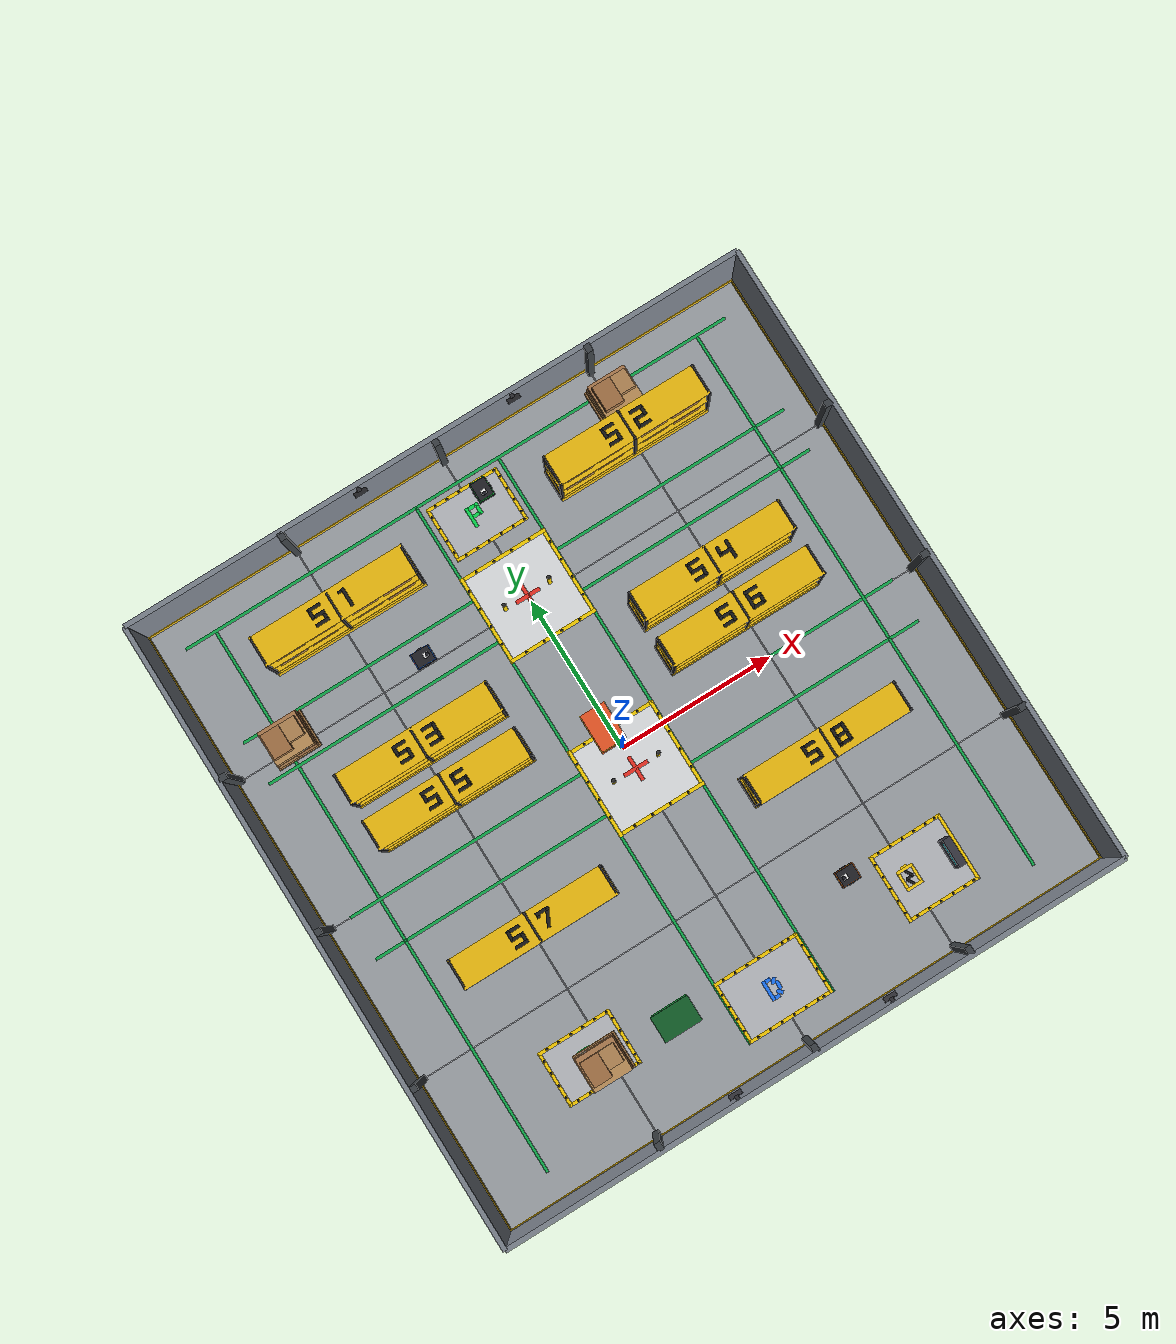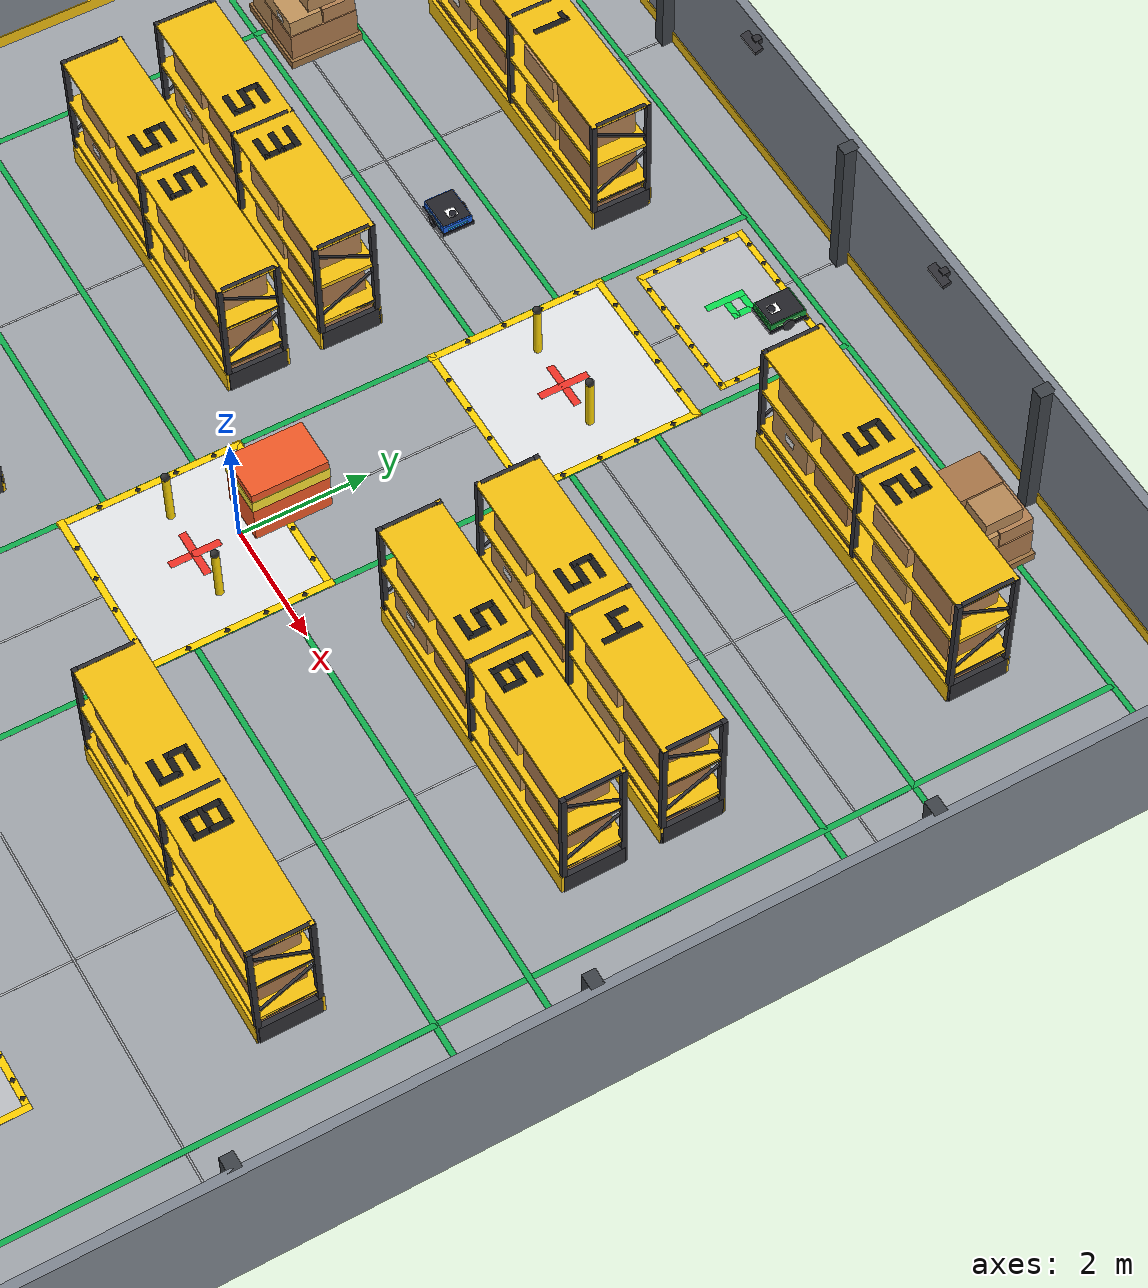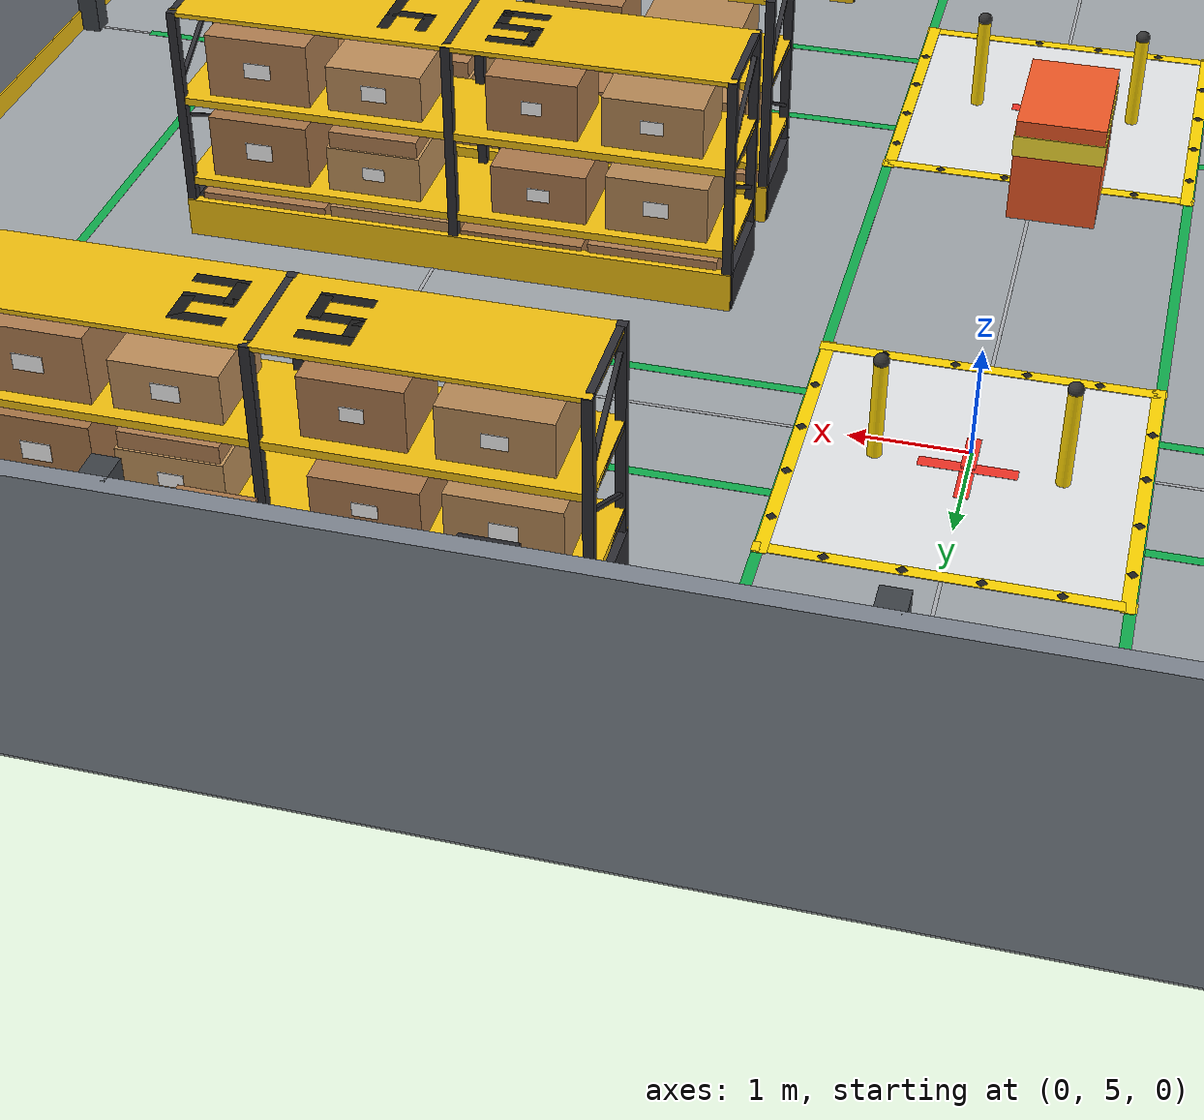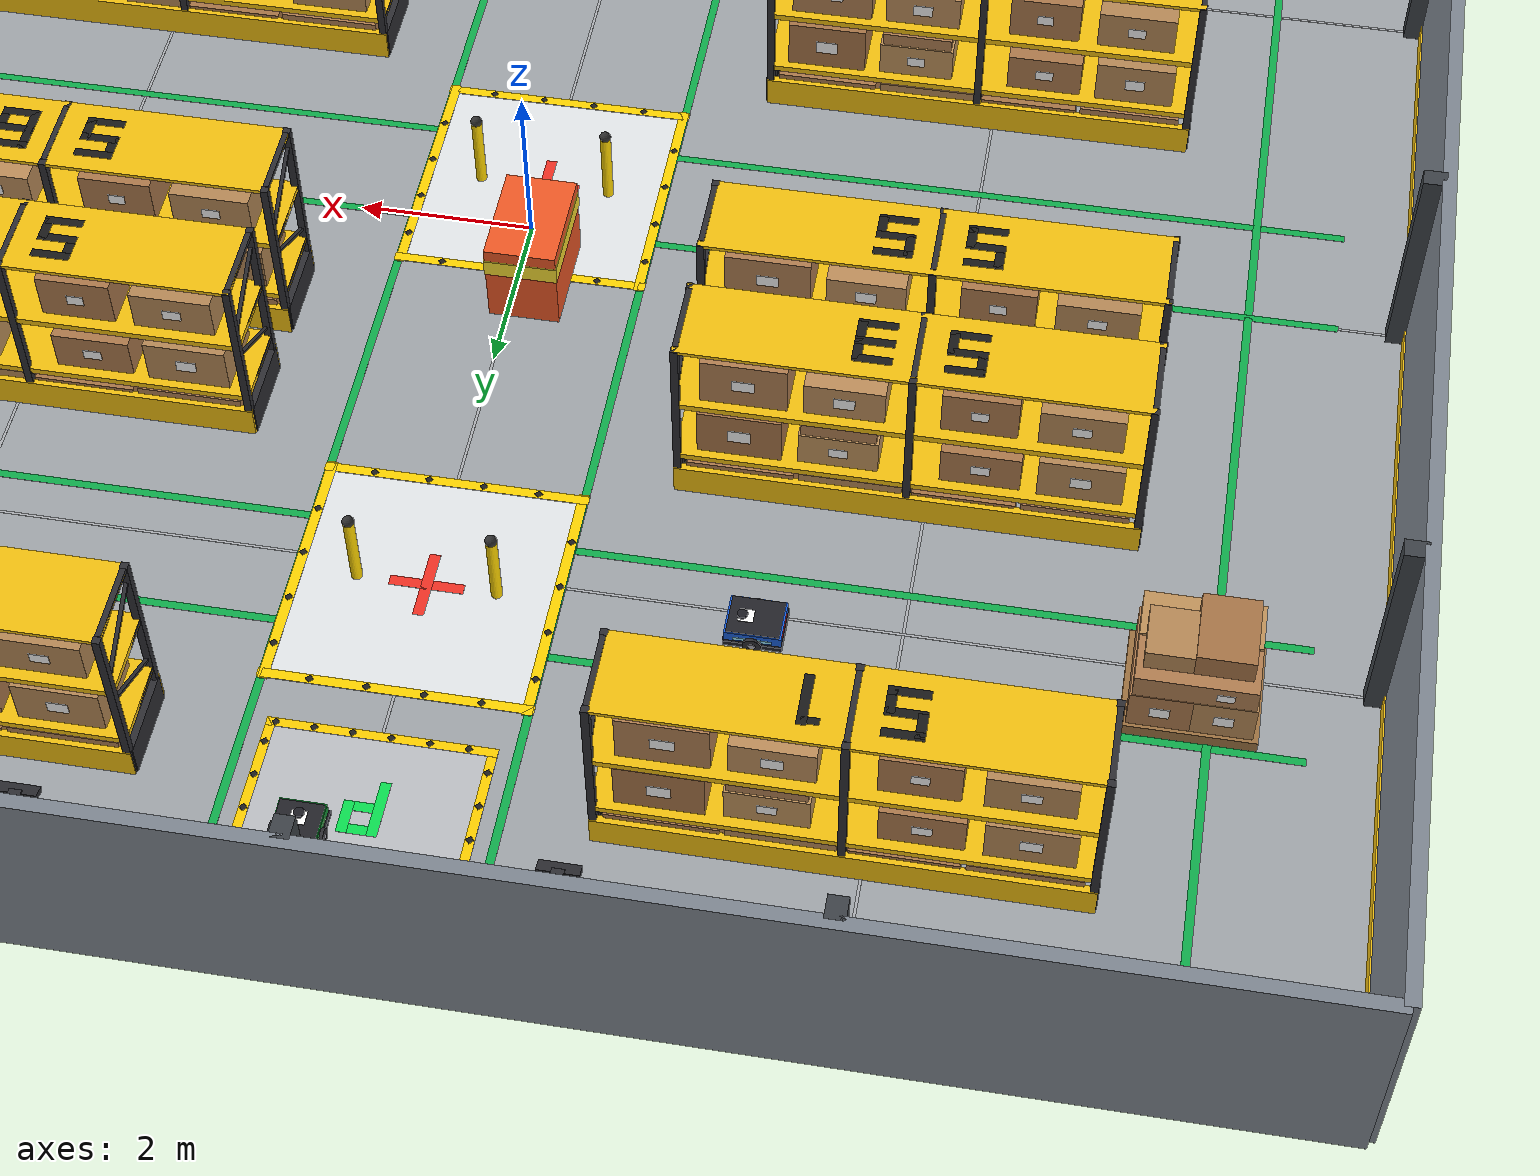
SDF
<?xml version="1.0"?>
<sdf version="1.9">
  <world name="warehouse">

    <!-- PHYSICS                                            -->
    <gravity>0 0 -9.81</gravity>
    <physics name="default_physics" type="ode">
      <max_step_size>0.001</max_step_size>
      <real_time_factor>1.0</real_time_factor>
      <real_time_update_rate>1000</real_time_update_rate>
    </physics>

    <plugin filename="gz-sim-physics-system"      name="gz::sim::systems::Physics"/>
    <plugin filename="gz-sim-sensors-system"      name="gz::sim::systems::Sensors"><render_engine>ogre2</render_engine></plugin>
    <plugin filename="gz-sim-scene-broadcaster-system" name="gz::sim::systems::SceneBroadcaster"/>
    <plugin filename="gz-sim-user-commands-system" name="gz::sim::systems::UserCommands"/>
    <plugin filename="gz-sim-contact-system"      name="gz::sim::systems::Contact"/>
    <plugin filename="gz-sim-imu-system"          name="gz::sim::systems::Imu"/>

    <!-- SCENE & LIGHTING                                  -->
    <scene>
      <ambient>0.60 0.61 0.64 1.0</ambient>
      <background>0.75 0.79 0.83 1.0</background>
      <shadows>true</shadows>
      <grid>false</grid>
    </scene>

    <!-- Primary Overhead Sun -->
    <light name="main_sun" type="directional">
      <pose>0 0 15 0 0 0</pose>
      <cast_shadows>true</cast_shadows>
      <diffuse>0.88 0.87 0.85 1.0</diffuse>
      <specular>0.28 0.28 0.28 1.0</specular>
      <direction>-0.2 0.15 -1.0</direction>
    </light>

    <!-- Warm Fill Bay Lights -->
    <light name="bay_n" type="point">
      <pose>-3.0 5.0 5.5 0 0 0</pose>
      <diffuse>0.50 0.49 0.47 1.0</diffuse>
      <attenuation><range>18</range><constant>0.4</constant><linear>0.05</linear></attenuation>
    </light>
    <light name="bay_s" type="point">
      <pose>3.0 -4.0 5.5 0 0 0</pose>
      <diffuse>0.50 0.49 0.47 1.0</diffuse>
      <attenuation><range>18</range><constant>0.4</constant><linear>0.05</linear></attenuation>
    </light>

    <!-- Wall Industrial Floodlights (Centered in wall bays at X = +-2.5m) -->
    <light name="wall_light_n1" type="point">
      <pose>-2.5 9.78 2.30 0 0 0</pose>
      <diffuse>0.38 0.38 0.35 1.0</diffuse>
      <attenuation><range>12</range><constant>0.6</constant><linear>0.08</linear></attenuation>
    </light>
    <light name="wall_light_n2" type="point">
      <pose>2.5 9.78 2.30 0 0 0</pose>
      <diffuse>0.38 0.38 0.35 1.0</diffuse>
      <attenuation><range>12</range><constant>0.6</constant><linear>0.08</linear></attenuation>
    </light>
    <light name="wall_light_s1" type="point">
      <pose>-2.5 -9.78 2.30 0 0 0</pose>
      <diffuse>0.38 0.38 0.35 1.0</diffuse>
      <attenuation><range>12</range><constant>0.6</constant><linear>0.08</linear></attenuation>
    </light>
    <light name="wall_light_s2" type="point">
      <pose>2.5 -9.78 2.30 0 0 0</pose>
      <diffuse>0.38 0.38 0.35 1.0</diffuse>
      <attenuation><range>12</range><constant>0.6</constant><linear>0.08</linear></attenuation>
    </light>

    <!-- FLOOR — Concrete with Grid Tile Lines              -->
    <model name="warehouse_floor">
      <static>true</static>
      <pose>0 0 -0.05 0 0 0</pose>
      <link name="floor_link">
        <collision name="col">
          <geometry><box><size>20.0 20.0 0.1</size></box></geometry>
          <surface><friction><ode><mu>1.0</mu><mu2>1.0</mu2></ode></friction></surface>
        </collision>
        <!-- Base Concrete Slab — slightly darker industrial grey -->
        <visual name="slab">
          <geometry><box><size>20.0 20.0 0.1</size></box></geometry>
          <material>
            <ambient>0.55 0.57 0.59 1.0</ambient>
            <diffuse>0.63 0.65 0.67 1.0</diffuse>
            <specular>0.10 0.10 0.10 1.0</specular>
          </material>
        </visual>

        <!-- === CONCRETE TILE GRID LINES (5m x 5m panels) === -->
        <!-- Horizontal lines at Y = -5, 0, +5, -->
        <visual name="grid_h1"><pose>0 -5.0 0.052 0 0 0</pose><geometry><box><size>20.0 0.03 0.002</size></box></geometry><material><ambient>0.62 0.63 0.65 1</ambient><diffuse>0.68 0.69 0.71 1</diffuse></material></visual>
        <visual name="grid_h2"><pose>0 0.0 0.052 0 0 0</pose><geometry><box><size>20.0 0.03 0.002</size></box></geometry><material><ambient>0.62 0.63 0.65 1</ambient><diffuse>0.68 0.69 0.71 1</diffuse></material></visual>
        <visual name="grid_h3"><pose>0 5.0 0.052 0 0 0</pose><geometry><box><size>20.0 0.03 0.002</size></box></geometry><material><ambient>0.62 0.63 0.65 1</ambient><diffuse>0.68 0.69 0.71 1</diffuse></material></visual>
        <!-- Vertical lines at X = -10, -5, 0, +5, +10 -->
        <visual name="grid_v1"><pose>-5.0 0 0.052 0 0 0</pose><geometry><box><size>0.03 20.0 0.002</size></box></geometry><material><ambient>0.62 0.63 0.65 1</ambient><diffuse>0.68 0.69 0.71 1</diffuse></material></visual>
        <visual name="grid_v2"><pose>0.0 0 0.052 0 0 0</pose><geometry><box><size>0.03 20.0 0.002</size></box></geometry><material><ambient>0.62 0.63 0.65 1</ambient><diffuse>0.68 0.69 0.71 1</diffuse></material></visual>
        <visual name="grid_v3"><pose>5.0 0 0.052 0 0 0</pose><geometry><box><size>0.03 20.0 0.002</size></box></geometry><material><ambient>0.62 0.63 0.65 1</ambient><diffuse>0.68 0.69 0.71 1</diffuse></material></visual>

        <!-- === GREEN SAFETY NAVIGATION LANES === -->
        <!-- Aisle 1 upper/lower -->
        <visual name="lane_a1_t"><pose>0 9.1 0.055 0 0 0</pose><geometry><box><size>18.4 0.09 0.002</size></box></geometry><material><ambient>0.04 0.52 0.22 1</ambient><diffuse>0.06 0.68 0.30 1</diffuse></material></visual>
        <visual name="lane_a1_b"><pose>0 5.9 0.055 0 0 0</pose><geometry><box><size>18.4 0.09 0.002</size></box></geometry><material><ambient>0.04 0.52 0.22 1</ambient><diffuse>0.06 0.68 0.30 1</diffuse></material></visual>
        <!-- Aisle 2 upper/lower -->
        <visual name="lane_a2_t"><pose>0 4.5 0.055 0 0 0</pose><geometry><box><size>18.4 0.09 0.002</size></box></geometry><material><ambient>0.04 0.52 0.22 1</ambient><diffuse>0.06 0.68 0.30 1</diffuse></material></visual>
        <visual name="lane_a2_b"><pose>0 0.0 0.055 0 0 0</pose><geometry><box><size>18.4 0.09 0.002</size></box></geometry><material><ambient>0.04 0.52 0.22 1</ambient><diffuse>0.06 0.68 0.30 1</diffuse></material></visual>
        <!-- Aisle 3 upper/lower -->
        <visual name="lane_a3_t"><pose>0 -1.4 0.055 0 0 0</pose><geometry><box><size>18.4 0.09 0.002</size></box></geometry><material><ambient>0.04 0.52 0.22 1</ambient><diffuse>0.06 0.68 0.30 1</diffuse></material></visual>

        <!-- Cross-corridor vertical lanes -->
        <visual name="lane_cv_l"><pose>-1.4 0 0.055 0 0 0</pose><geometry><box><size>0.09 18.2 0.002</size></box></geometry><material><ambient>0.04 0.52 0.22 1</ambient><diffuse>0.06 0.68 0.30 1</diffuse></material></visual>
        <visual name="lane_cv_r"><pose>1.4 0 0.055 0 0 0</pose><geometry><box><size>0.09 18.2 0.002</size></box></geometry><material><ambient>0.04 0.52 0.22 1</ambient><diffuse>0.06 0.68 0.30 1</diffuse></material></visual>
        <!-- Outer bypass lanes -->
        <visual name="lane_bp_w"><pose>-8.2 0 0.055 0 0 0</pose><geometry><box><size>0.09 18.2 0.002</size></box></geometry><material><ambient>0.04 0.52 0.22 1</ambient><diffuse>0.06 0.68 0.30 1</diffuse></material></visual>
        <visual name="lane_bp_e"><pose>8.2 0 0.055 0 0 0</pose><geometry><box><size>0.09 18.2 0.002</size></box></geometry><material><ambient>0.04 0.52 0.22 1</ambient><diffuse>0.06 0.68 0.30 1</diffuse></material></visual>
      </link>
    </model>

    <!-- PERIMETER WALLS WITH YELLOW SKIRTING              -->
    <model name="north_wall">
      <static>true</static>
      <pose>0 10 1.25 0 0 0</pose>
      <link name="link">
        <collision name="col"><geometry><box><size>20.0 0.15 2.5</size></box></geometry></collision>
        <visual name="vis"><geometry><box><size>20.0 0.15 2.5</size></box></geometry><material><ambient>0.40 0.43 0.46 1</ambient><diffuse>0.50 0.53 0.57 1</diffuse></material></visual>
        <visual name="skirt"><pose>0 -0.08 -1.15 0 0 0</pose><geometry><box><size>20.0 0.025 0.22</size></box></geometry><material><ambient>0.88 0.68 0.04 1</ambient><diffuse>0.96 0.76 0.06 1</diffuse></material></visual>
      </link>
    </model>
    <model name="south_wall">
      <static>true</static>
      <pose>0 -10 1.25 0 0 0</pose>
      <link name="link">
        <collision name="col"><geometry><box><size>20.0 0.15 2.5</size></box></geometry></collision>
        <visual name="vis"><geometry><box><size>20.0 0.15 2.5</size></box></geometry><material><ambient>0.40 0.43 0.46 1</ambient><diffuse>0.50 0.53 0.57 1</diffuse></material></visual>
        <visual name="skirt"><pose>0 0.08 -1.15 0 0 0</pose><geometry><box><size>20.0 0.025 0.22</size></box></geometry><material><ambient>0.88 0.68 0.04 1</ambient><diffuse>0.96 0.76 0.06 1</diffuse></material></visual>
      </link>
    </model>
    <model name="east_wall">
      <static>true</static>
      <pose>10.0 0 1.25 0 0 0</pose>
      <link name="link">
        <collision name="col"><geometry><box><size>0.15 20.0 2.5</size></box></geometry></collision>
        <visual name="vis"><geometry><box><size>0.15 20.0 2.5</size></box></geometry><material><ambient>0.40 0.43 0.46 1</ambient><diffuse>0.50 0.53 0.57 1</diffuse></material></visual>
        <visual name="skirt"><pose>-0.08 0 -1.15 0 0 0</pose><geometry><box><size>0.025 20.0 0.22</size></box></geometry><material><ambient>0.88 0.68 0.04 1</ambient><diffuse>0.96 0.76 0.06 1</diffuse></material></visual>
      </link>
    </model>
    <model name="west_wall">
      <static>true</static>
      <pose>-10.0 0 1.25 0 0 0</pose>
      <link name="link">
        <collision name="col"><geometry><box><size>0.15 20.0 2.5</size></box></geometry></collision>
        <visual name="vis"><geometry><box><size>0.15 20.0 2.5</size></box></geometry><material><ambient>0.40 0.43 0.46 1</ambient><diffuse>0.50 0.53 0.57 1</diffuse></material></visual>
        <visual name="skirt"><pose>0.08 0 -1.15 0 0 0</pose><geometry><box><size>0.025 20.0 0.22</size></box></geometry><material><ambient>0.88 0.68 0.04 1</ambient><diffuse>0.96 0.76 0.06 1</diffuse></material></visual>
      </link>
    </model>

    <!-- STRUCTURAL WALL PILLAR COLUMNS (every ~5m)         -->
    <!-- Industrial I-beam columns, anthracite steel        -->
    <!-- North wall pillars -->
    <model name="pillar_n_l"><static>true</static><pose>-5.0 9.85 1.25 0 0 0</pose><link name="link"><visual name="vis"><geometry><box><size>0.20 0.25 2.5</size></box></geometry><material><ambient>0.18 0.20 0.22 1</ambient><diffuse>0.24 0.26 0.28 1</diffuse></material></visual></link></model>
    <model name="pillar_n_r"><static>true</static><pose>5.0 9.85 1.25 0 0 0</pose><link name="link"><visual name="vis"><geometry><box><size>0.20 0.25 2.5</size></box></geometry><material><ambient>0.18 0.20 0.22 1</ambient><diffuse>0.24 0.26 0.28 1</diffuse></material></visual></link></model>
    <model name="pillar_n_c"><static>true</static><pose>0.0 9.85 1.25 0 0 0</pose><link name="link"><visual name="vis"><geometry><box><size>0.20 0.25 2.5</size></box></geometry><material><ambient>0.18 0.20 0.22 1</ambient><diffuse>0.24 0.26 0.28 1</diffuse></material></visual></link></model>
    <!-- South wall pillars -->
    <model name="pillar_s_l"><static>true</static><pose>-5.0 -9.85 1.25 0 0 0</pose><link name="link"><visual name="vis"><geometry><box><size>0.20 0.25 2.5</size></box></geometry><material><ambient>0.18 0.20 0.22 1</ambient><diffuse>0.24 0.26 0.28 1</diffuse></material></visual></link></model>
    <model name="pillar_s_r"><static>true</static><pose>5.0 -9.85 1.25 0 0 0</pose><link name="link"><visual name="vis"><geometry><box><size>0.20 0.25 2.5</size></box></geometry><material><ambient>0.18 0.20 0.22 1</ambient><diffuse>0.24 0.26 0.28 1</diffuse></material></visual></link></model>
    <model name="pillar_s_c"><static>true</static><pose>0.0 -9.85 1.25 0 0 0</pose><link name="link"><visual name="vis"><geometry><box><size>0.20 0.25 2.5</size></box></geometry><material><ambient>0.18 0.20 0.22 1</ambient><diffuse>0.24 0.26 0.28 1</diffuse></material></visual></link></model>
    <!-- East wall pillars -->
    <model name="pillar_e_n"><static>true</static><pose>9.85 5.00 1.25 0 0 0</pose><link name="link"><visual name="vis"><geometry><box><size>0.25 0.20 2.5</size></box></geometry><material><ambient>0.18 0.20 0.22 1</ambient><diffuse>0.24 0.26 0.28 1</diffuse></material></visual></link></model>
    <model name="pillar_e_s"><static>true</static><pose>9.85 -5.00 1.25 0 0 0</pose><link name="link"><visual name="vis"><geometry><box><size>0.25 0.20 2.5</size></box></geometry><material><ambient>0.18 0.20 0.22 1</ambient><diffuse>0.24 0.26 0.28 1</diffuse></material></visual></link></model>
    <model name="pillar_e_c"><static>true</static><pose>9.85 0.0 1.25 0 0 0</pose><link name="link"><visual name="vis"><geometry><box><size>0.25 0.20 2.5</size></box></geometry><material><ambient>0.18 0.20 0.22 1</ambient><diffuse>0.24 0.26 0.28 1</diffuse></material></visual></link></model>
    <!-- West wall pillars -->
    <model name="pillar_w_n"><static>true</static><pose>-9.85 5.00 1.25 0 0 0</pose><link name="link"><visual name="vis"><geometry><box><size>0.25 0.20 2.5</size></box></geometry><material><ambient>0.18 0.20 0.22 1</ambient><diffuse>0.24 0.26 0.28 1</diffuse></material></visual></link></model>
    <model name="pillar_w_s"><static>true</static><pose>-9.85 -5.00 1.25 0 0 0</pose><link name="link"><visual name="vis"><geometry><box><size>0.25 0.20 2.5</size></box></geometry><material><ambient>0.18 0.20 0.22 1</ambient><diffuse>0.24 0.26 0.28 1</diffuse></material></visual></link></model>
    <model name="pillar_w_c"><static>true</static><pose>-9.85 0.0 1.25 0 0 0</pose><link name="link"><visual name="vis"><geometry><box><size>0.25 0.20 2.5</size></box></geometry><material><ambient>0.18 0.20 0.22 1</ambient><diffuse>0.24 0.26 0.28 1</diffuse></material></visual></link></model>

    <!-- Wall-Mounted Industrial LED Lighting Fixtures (Centered in wall bays at X = +-2.5m) -->
    <!-- North Wall Fixtures -->
    <model name="fixture_wall_n1"><static>true</static><pose>-2.5 9.92 2.35 0 0 0</pose>
      <link name="link">
        <visual name="bracket"><pose>0 -0.06 0 0 0 0</pose><geometry><box><size>0.12 0.12 0.08</size></box></geometry><material><ambient>0.12 0.12 0.14 1</ambient><diffuse>0.18 0.18 0.20 1</diffuse></material></visual>
        <visual name="lamp"><pose>0 -0.14 -0.02 0.3 0 0</pose><geometry><box><size>0.40 0.14 0.06</size></box></geometry><material><ambient>0.12 0.12 0.14 1</ambient><diffuse>0.18 0.18 0.20 1</diffuse></material></visual>
        <visual name="led_strip"><pose>0 -0.14 -0.05 0.3 0 0</pose><geometry><box><size>0.36 0.10 0.01</size></box></geometry><material><ambient>0.9 0.9 0.85 1</ambient><diffuse>1.0 1.0 0.9 1</diffuse><emissive>0.95 0.95 0.85 1</emissive></material></visual>
      </link></model>
    <model name="fixture_wall_n2"><static>true</static><pose>2.5 9.92 2.35 0 0 0</pose>
      <link name="link">
        <visual name="bracket"><pose>0 -0.06 0 0 0 0</pose><geometry><box><size>0.12 0.12 0.08</size></box></geometry><material><ambient>0.12 0.12 0.14 1</ambient><diffuse>0.18 0.18 0.20 1</diffuse></material></visual>
        <visual name="lamp"><pose>0 -0.14 -0.02 0.3 0 0</pose><geometry><box><size>0.40 0.14 0.06</size></box></geometry><material><ambient>0.12 0.12 0.14 1</ambient><diffuse>0.18 0.18 0.20 1</diffuse></material></visual>
        <visual name="led_strip"><pose>0 -0.14 -0.05 0.3 0 0</pose><geometry><box><size>0.36 0.10 0.01</size></box></geometry><material><ambient>0.9 0.9 0.85 1</ambient><diffuse>1.0 1.0 0.9 1</diffuse><emissive>0.95 0.95 0.85 1</emissive></material></visual>
      </link></model>
    <!-- South Wall Fixtures -->
    <model name="fixture_wall_s1"><static>true</static><pose>-2.5 -9.92 2.35 0 0 3.14159</pose>
      <link name="link">
        <visual name="bracket"><pose>0 -0.06 0 0 0 0</pose><geometry><box><size>0.12 0.12 0.08</size></box></geometry><material><ambient>0.12 0.12 0.14 1</ambient><diffuse>0.18 0.18 0.20 1</diffuse></material></visual>
        <visual name="lamp"><pose>0 -0.14 -0.02 0.3 0 0</pose><geometry><box><size>0.40 0.14 0.06</size></box></geometry><material><ambient>0.12 0.12 0.14 1</ambient><diffuse>0.18 0.18 0.20 1</diffuse></material></visual>
        <visual name="led_strip"><pose>0 -0.14 -0.05 0.3 0 0</pose><geometry><box><size>0.36 0.10 0.01</size></box></geometry><material><ambient>0.9 0.9 0.85 1</ambient><diffuse>1.0 1.0 0.9 1</diffuse><emissive>0.95 0.95 0.85 1</emissive></material></visual>
      </link></model>
    <model name="fixture_wall_s2"><static>true</static><pose>2.5 -9.92 2.35 0 0 3.14159</pose>
      <link name="link">
        <visual name="bracket"><pose>0 -0.06 0 0 0 0</pose><geometry><box><size>0.12 0.12 0.08</size></box></geometry><material><ambient>0.12 0.12 0.14 1</ambient><diffuse>0.18 0.18 0.20 1</diffuse></material></visual>
        <visual name="lamp"><pose>0 -0.14 -0.02 0.3 0 0</pose><geometry><box><size>0.40 0.14 0.06</size></box></geometry><material><ambient>0.12 0.12 0.14 1</ambient><diffuse>0.18 0.18 0.20 1</diffuse></material></visual>
        <visual name="led_strip"><pose>0 -0.14 -0.05 0.3 0 0</pose><geometry><box><size>0.36 0.10 0.01</size></box></geometry><material><ambient>0.9 0.9 0.85 1</ambient><diffuse>1.0 1.0 0.9 1</diffuse><emissive>0.95 0.95 0.85 1</emissive></material></visual>
      </link></model>

    <!-- INDUSTRIAL RACK SHELVING (NW, NE, SW, SE)         -->
    <include>
      <uri>model://shelf</uri>
      <name>shelf_rack_NW1</name>
      <pose>-4.8 7.5 0 0 0 0</pose>
    </include>
    <include>
      <uri>model://shelf</uri>
      <name>shelf_rack_NE1</name>
      <pose>4.8 7.5 0 0 0 0</pose>
    </include>
    <include>
      <uri>model://shelf</uri>
      <name>shelf_rack_NW2</name>
      <pose>-4.8 3.0 0 0 0 0</pose>
    </include>
    <include>
      <uri>model://shelf</uri>
      <name>shelf_rack_NE2</name>
      <pose>4.8 3.0 0 0 0 0</pose>
    </include>
    <include>
      <uri>model://shelf</uri>
      <name>shelf_rack_SW2</name>
      <pose>-4.8 1.5 0 0 0 0</pose>
    </include>
    <include>
      <uri>model://shelf</uri>
      <name>shelf_rack_SE2</name>
      <pose>4.8 1.5 0 0 0 0</pose>
    </include>
    <include>
      <uri>model://shelf</uri>
      <name>shelf_rack_SW1</name>
      <pose>-4.8 -3.0 0 0 0 0</pose>
    </include>
    <include>
      <uri>model://shelf</uri>
      <name>shelf_rack_SE1</name>
      <pose>4.8 -3.0 0 0 0 0</pose>
    </include>

    <!-- LOGISTICS PROPS                                    -->
    <include>
      <uri>model://pallet_stack</uri>
      <name>pallet_tower_1</name>
      <pose>-5.2 -7.3 0 0 0 0</pose>
    </include>
    <include>
      <uri>model://pallet_stack</uri>
      <name>pallet_tower_2</name>
      <pose>5.2 8.75 0 0 0 0</pose>
    </include>
    <!-- Extra scattered box near NW aisle entrance -->
    <include>
      <uri>model://pallet_stack</uri>
      <name>pallet_tower_3</name>
      <pose>-8.0 5.25 0 0 0 0</pose>
    </include>
    <include>
      <uri>model://dumpster</uri>
      <name>green_dumpster_container</name>
      <pose>-2.8 -7.3 0 0 0 0</pose>
    </include>

    <!-- INTERSECTION I1 & I2 — PROMINENT CONFLICT ZONE          -->

    <!-- Intersection I1 -->
    <model name="intersection_I1_marker">
      <static>true</static>
      <pose>0 5.2 0.005 0 0 0</pose>
      <link name="link">
        <!-- Bright contrast base zone -->
        <visual name="marker_zone">
          <geometry><box><size>2.7 2.7 0.005</size></box></geometry>
          <material><ambient>0.82 0.83 0.84 1.0</ambient><diffuse>0.90 0.91 0.92 1.0</diffuse></material>
        </visual>

        <!-- Yellow outer frame -->
        <visual name="frame_n"><pose>0 1.38 0.006 0 0 0</pose><geometry><box><size>2.9 0.11 0.006</size></box></geometry><material><ambient>0.95 0.78 0.0 1</ambient><diffuse>1.0 0.84 0.0 1</diffuse></material></visual>
        <visual name="frame_s"><pose>0 -1.38 0.006 0 0 0</pose><geometry><box><size>2.9 0.11 0.006</size></box></geometry><material><ambient>0.95 0.78 0.0 1</ambient><diffuse>1.0 0.84 0.0 1</diffuse></material></visual>
        <visual name="frame_e"><pose>1.38 0 0.006 0 0 0</pose><geometry><box><size>0.11 2.9 0.006</size></box></geometry><material><ambient>0.95 0.78 0.0 1</ambient><diffuse>1.0 0.84 0.0 1</diffuse></material></visual>
        <visual name="frame_w"><pose>-1.38 0 0.006 0 0 0</pose><geometry><box><size>0.11 2.9 0.006</size></box></geometry><material><ambient>0.95 0.78 0.0 1</ambient><diffuse>1.0 0.84 0.0 1</diffuse></material></visual>

        <!-- Black diagonal hazard stripes at 45° on all 4 sides -->
        <visual name="hz_n1"><pose>-0.9 1.38 0.007 0 0 0.7854</pose><geometry><box><size>0.065 0.065 0.006</size></box></geometry><material><ambient>0.08 0.08 0.08 1</ambient><diffuse>0.12 0.12 0.12 1</diffuse></material></visual>
        <visual name="hz_n2"><pose>-0.3 1.38 0.007 0 0 0.7854</pose><geometry><box><size>0.065 0.065 0.006</size></box></geometry><material><ambient>0.08 0.08 0.08 1</ambient><diffuse>0.12 0.12 0.12 1</diffuse></material></visual>
        <visual name="hz_n3"><pose>0.3 1.38 0.007 0 0 0.7854</pose><geometry><box><size>0.065 0.065 0.006</size></box></geometry><material><ambient>0.08 0.08 0.08 1</ambient><diffuse>0.12 0.12 0.12 1</diffuse></material></visual>
        <visual name="hz_n4"><pose>0.9 1.38 0.007 0 0 0.7854</pose><geometry><box><size>0.065 0.065 0.006</size></box></geometry><material><ambient>0.08 0.08 0.08 1</ambient><diffuse>0.12 0.12 0.12 1</diffuse></material></visual>
        <visual name="hz_s1"><pose>-0.9 -1.38 0.007 0 0 0.7854</pose><geometry><box><size>0.065 0.065 0.006</size></box></geometry><material><ambient>0.08 0.08 0.08 1</ambient><diffuse>0.12 0.12 0.12 1</diffuse></material></visual>
        <visual name="hz_s2"><pose>-0.3 -1.38 0.007 0 0 0.7854</pose><geometry><box><size>0.065 0.065 0.006</size></box></geometry><material><ambient>0.08 0.08 0.08 1</ambient><diffuse>0.12 0.12 0.12 1</diffuse></material></visual>
        <visual name="hz_s3"><pose>0.3 -1.38 0.007 0 0 0.7854</pose><geometry><box><size>0.065 0.065 0.006</size></box></geometry><material><ambient>0.08 0.08 0.08 1</ambient><diffuse>0.12 0.12 0.12 1</diffuse></material></visual>
        <visual name="hz_s4"><pose>0.9 -1.38 0.007 0 0 0.7854</pose><geometry><box><size>0.065 0.065 0.006</size></box></geometry><material><ambient>0.08 0.08 0.08 1</ambient><diffuse>0.12 0.12 0.12 1</diffuse></material></visual>
        <visual name="hz_e1"><pose>1.38 -0.8 0.007 0 0 0.7854</pose><geometry><box><size>0.065 0.065 0.006</size></box></geometry><material><ambient>0.08 0.08 0.08 1</ambient><diffuse>0.12 0.12 0.12 1</diffuse></material></visual>
        <visual name="hz_e2"><pose>1.38 -0.2 0.007 0 0 0.7854</pose><geometry><box><size>0.065 0.065 0.006</size></box></geometry><material><ambient>0.08 0.08 0.08 1</ambient><diffuse>0.12 0.12 0.12 1</diffuse></material></visual>
        <visual name="hz_e3"><pose>1.38 0.4 0.007 0 0 0.7854</pose><geometry><box><size>0.065 0.065 0.006</size></box></geometry><material><ambient>0.08 0.08 0.08 1</ambient><diffuse>0.12 0.12 0.12 1</diffuse></material></visual>
        <visual name="hz_e4"><pose>1.38 1.0 0.007 0 0 0.7854</pose><geometry><box><size>0.065 0.065 0.006</size></box></geometry><material><ambient>0.08 0.08 0.08 1</ambient><diffuse>0.12 0.12 0.12 1</diffuse></material></visual>
        <visual name="hz_w1"><pose>-1.38 -0.8 0.007 0 0 0.7854</pose><geometry><box><size>0.065 0.065 0.006</size></box></geometry><material><ambient>0.08 0.08 0.08 1</ambient><diffuse>0.12 0.12 0.12 1</diffuse></material></visual>
        <visual name="hz_w2"><pose>-1.38 -0.2 0.007 0 0 0.7854</pose><geometry><box><size>0.065 0.065 0.006</size></box></geometry><material><ambient>0.08 0.08 0.08 1</ambient><diffuse>0.12 0.12 0.12 1</diffuse></material></visual>
        <visual name="hz_w3"><pose>-1.38 0.4 0.007 0 0 0.7854</pose><geometry><box><size>0.065 0.065 0.006</size></box></geometry><material><ambient>0.08 0.08 0.08 1</ambient><diffuse>0.12 0.12 0.12 1</diffuse></material></visual>
        <visual name="hz_w4"><pose>-1.38 1.0 0.007 0 0 0.7854</pose><geometry><box><size>0.065 0.065 0.006</size></box></geometry><material><ambient>0.08 0.08 0.08 1</ambient><diffuse>0.12 0.12 0.12 1</diffuse></material></visual>

        <!-- "I1" zone label — flush painted red cross marker -->
        <visual name="i1_cross_h"><pose>0 0 0.005 0 0 0</pose><geometry><box><size>0.80 0.12 0.0015</size></box></geometry><material><ambient>0.85 0.15 0.10 1</ambient><diffuse>0.95 0.2 0.15 1</diffuse></material></visual>
        <visual name="i1_cross_v"><pose>0 0 0.005 0 0 0</pose><geometry><box><size>0.12 0.80 0.0015</size></box></geometry><material><ambient>0.85 0.15 0.10 1</ambient><diffuse>0.95 0.2 0.15 1</diffuse></material></visual>
      </link>
    </model>

    <!-- Choke Bollards at I1 -->
    <model name="bollard_l1">
      <static>true</static><pose>-0.75 5.2 0.45 0 0 0</pose>
      <link name="link">
        <collision name="col"><geometry><cylinder><radius>0.06</radius><length>0.9</length></cylinder></geometry></collision>
        <visual name="vis"><geometry><cylinder><radius>0.06</radius><length>0.9</length></cylinder></geometry><material><ambient>0.95 0.78 0.0 1</ambient><diffuse>1.0 0.84 0.0 1</diffuse></material></visual>
        <visual name="cap"><pose>0 0 0.46 0 0 0</pose><geometry><sphere><radius>0.065</radius></sphere></geometry><material><ambient>0.15 0.15 0.15 1</ambient><diffuse>0.20 0.20 0.20 1</diffuse></material></visual>
      </link>
    </model>
    <model name="bollard_r1">
      <static>true</static><pose>0.75 5.2 0.45 0 0 0</pose>
      <link name="link">
        <collision name="col"><geometry><cylinder><radius>0.06</radius><length>0.9</length></cylinder></geometry></collision>
        <visual name="vis"><geometry><cylinder><radius>0.06</radius><length>0.9</length></cylinder></geometry><material><ambient>0.95 0.78 0.0 1</ambient><diffuse>1.0 0.84 0.0 1</diffuse></material></visual>
        <visual name="cap"><pose>0 0 0.46 0 0 0</pose><geometry><sphere><radius>0.065</radius></sphere></geometry><material><ambient>0.15 0.15 0.15 1</ambient><diffuse>0.20 0.20 0.20 1</diffuse></material></visual>
      </link>
    </model>

    <!-- Intersection I2 -->
    <model name="intersection_I2_marker">
      <static>true</static>
      <pose>0 -0.7 0.005 0 0 0</pose>
      <link name="link">
        <!-- Bright contrast base zone -->
        <visual name="marker_zone">
          <geometry><box><size>2.7 2.7 0.005</size></box></geometry>
          <material><ambient>0.82 0.83 0.84 1.0</ambient><diffuse>0.90 0.91 0.92 1.0</diffuse></material>
        </visual>

        <!-- Yellow outer frame -->
        <visual name="frame_n"><pose>0 1.38 0.006 0 0 0</pose><geometry><box><size>2.9 0.11 0.006</size></box></geometry><material><ambient>0.95 0.78 0.0 1</ambient><diffuse>1.0 0.84 0.0 1</diffuse></material></visual>
        <visual name="frame_s"><pose>0 -1.38 0.006 0 0 0</pose><geometry><box><size>2.9 0.11 0.006</size></box></geometry><material><ambient>0.95 0.78 0.0 1</ambient><diffuse>1.0 0.84 0.0 1</diffuse></material></visual>
        <visual name="frame_e"><pose>1.38 0 0.006 0 0 0</pose><geometry><box><size>0.11 2.9 0.006</size></box></geometry><material><ambient>0.95 0.78 0.0 1</ambient><diffuse>1.0 0.84 0.0 1</diffuse></material></visual>
        <visual name="frame_w"><pose>-1.38 0 0.006 0 0 0</pose><geometry><box><size>0.11 2.9 0.006</size></box></geometry><material><ambient>0.95 0.78 0.0 1</ambient><diffuse>1.0 0.84 0.0 1</diffuse></material></visual>

        <!-- Black diagonal hazard stripes at 45° on all 4 sides -->
        <visual name="hz_n1"><pose>-0.9 1.38 0.007 0 0 0.7854</pose><geometry><box><size>0.065 0.065 0.006</size></box></geometry><material><ambient>0.08 0.08 0.08 1</ambient><diffuse>0.12 0.12 0.12 1</diffuse></material></visual>
        <visual name="hz_n2"><pose>-0.3 1.38 0.007 0 0 0.7854</pose><geometry><box><size>0.065 0.065 0.006</size></box></geometry><material><ambient>0.08 0.08 0.08 1</ambient><diffuse>0.12 0.12 0.12 1</diffuse></material></visual>
        <visual name="hz_n3"><pose>0.3 1.38 0.007 0 0 0.7854</pose><geometry><box><size>0.065 0.065 0.006</size></box></geometry><material><ambient>0.08 0.08 0.08 1</ambient><diffuse>0.12 0.12 0.12 1</diffuse></material></visual>
        <visual name="hz_n4"><pose>0.9 1.38 0.007 0 0 0.7854</pose><geometry><box><size>0.065 0.065 0.006</size></box></geometry><material><ambient>0.08 0.08 0.08 1</ambient><diffuse>0.12 0.12 0.12 1</diffuse></material></visual>
        <visual name="hz_s1"><pose>-0.9 -1.38 0.007 0 0 0.7854</pose><geometry><box><size>0.065 0.065 0.006</size></box></geometry><material><ambient>0.08 0.08 0.08 1</ambient><diffuse>0.12 0.12 0.12 1</diffuse></material></visual>
        <visual name="hz_s2"><pose>-0.3 -1.38 0.007 0 0 0.7854</pose><geometry><box><size>0.065 0.065 0.006</size></box></geometry><material><ambient>0.08 0.08 0.08 1</ambient><diffuse>0.12 0.12 0.12 1</diffuse></material></visual>
        <visual name="hz_s3"><pose>0.3 -1.38 0.007 0 0 0.7854</pose><geometry><box><size>0.065 0.065 0.006</size></box></geometry><material><ambient>0.08 0.08 0.08 1</ambient><diffuse>0.12 0.12 0.12 1</diffuse></material></visual>
        <visual name="hz_s4"><pose>0.9 -1.38 0.007 0 0 0.7854</pose><geometry><box><size>0.065 0.065 0.006</size></box></geometry><material><ambient>0.08 0.08 0.08 1</ambient><diffuse>0.12 0.12 0.12 1</diffuse></material></visual>
        <visual name="hz_e1"><pose>1.38 -0.8 0.007 0 0 0.7854</pose><geometry><box><size>0.065 0.065 0.006</size></box></geometry><material><ambient>0.08 0.08 0.08 1</ambient><diffuse>0.12 0.12 0.12 1</diffuse></material></visual>
        <visual name="hz_e2"><pose>1.38 -0.2 0.007 0 0 0.7854</pose><geometry><box><size>0.065 0.065 0.006</size></box></geometry><material><ambient>0.08 0.08 0.08 1</ambient><diffuse>0.12 0.12 0.12 1</diffuse></material></visual>
        <visual name="hz_e3"><pose>1.38 0.4 0.007 0 0 0.7854</pose><geometry><box><size>0.065 0.065 0.006</size></box></geometry><material><ambient>0.08 0.08 0.08 1</ambient><diffuse>0.12 0.12 0.12 1</diffuse></material></visual>
        <visual name="hz_e4"><pose>1.38 1.0 0.007 0 0 0.7854</pose><geometry><box><size>0.065 0.065 0.006</size></box></geometry><material><ambient>0.08 0.08 0.08 1</ambient><diffuse>0.12 0.12 0.12 1</diffuse></material></visual>
        <visual name="hz_w1"><pose>-1.38 -0.8 0.007 0 0 0.7854</pose><geometry><box><size>0.065 0.065 0.006</size></box></geometry><material><ambient>0.08 0.08 0.08 1</ambient><diffuse>0.12 0.12 0.12 1</diffuse></material></visual>
        <visual name="hz_w2"><pose>-1.38 -0.2 0.007 0 0 0.7854</pose><geometry><box><size>0.065 0.065 0.006</size></box></geometry><material><ambient>0.08 0.08 0.08 1</ambient><diffuse>0.12 0.12 0.12 1</diffuse></material></visual>
        <visual name="hz_w3"><pose>-1.38 0.4 0.007 0 0 0.7854</pose><geometry><box><size>0.065 0.065 0.006</size></box></geometry><material><ambient>0.08 0.08 0.08 1</ambient><diffuse>0.12 0.12 0.12 1</diffuse></material></visual>
        <visual name="hz_w4"><pose>-1.38 1.0 0.007 0 0 0.7854</pose><geometry><box><size>0.065 0.065 0.006</size></box></geometry><material><ambient>0.08 0.08 0.08 1</ambient><diffuse>0.12 0.12 0.12 1</diffuse></material></visual>

        <!-- "I2" zone label — flush painted red cross marker -->
        <visual name="i2_cross_h"><pose>0 0 0.005 0 0 0</pose><geometry><box><size>0.80 0.12 0.0015</size></box></geometry><material><ambient>0.85 0.15 0.10 1</ambient><diffuse>0.95 0.2 0.15 1</diffuse></material></visual>
        <visual name="i2_cross_v"><pose>0 0 0.005 0 0 0</pose><geometry><box><size>0.12 0.80 0.0015</size></box></geometry><material><ambient>0.85 0.15 0.10 1</ambient><diffuse>0.95 0.2 0.15 1</diffuse></material></visual>
      </link>
    </model>

    <!-- Choke Bollards at I2 -->
    <model name="bollard_l2">
      <static>true</static><pose>-0.75 -0.7 0.45 0 0 0</pose>
      <link name="link">
        <collision name="col"><geometry><cylinder><radius>0.06</radius><length>0.9</length></cylinder></geometry></collision>
        <visual name="vis"><geometry><cylinder><radius>0.06</radius><length>0.9</length></cylinder></geometry><material><ambient>0.95 0.78 0.0 1</ambient><diffuse>1.0 0.84 0.0 1</diffuse></material></visual>
        <visual name="cap"><pose>0 0 0.46 0 0 0</pose><geometry><sphere><radius>0.065</radius></sphere></geometry><material><ambient>0.15 0.15 0.15 1</ambient><diffuse>0.20 0.20 0.20 1</diffuse></material></visual>
      </link>
    </model>
    <model name="bollard_r2">
      <static>true</static><pose>0.75 -0.7 0.45 0 0 0</pose>
      <link name="link">
        <collision name="col"><geometry><cylinder><radius>0.06</radius><length>0.9</length></cylinder></geometry></collision>
        <visual name="vis"><geometry><cylinder><radius>0.06</radius><length>0.9</length></cylinder></geometry><material><ambient>0.95 0.78 0.0 1</ambient><diffuse>1.0 0.84 0.0 1</diffuse></material></visual>
        <visual name="cap"><pose>0 0 0.46 0 0 0</pose><geometry><sphere><radius>0.065</radius></sphere></geometry><material><ambient>0.15 0.15 0.15 1</ambient><diffuse>0.20 0.20 0.20 1</diffuse></material></visual>
      </link>
    </model>

    <!-- ZONE LETTER SIGNS (floor) + SHELF NUMBER SIGNS (top) -->
    <!-- Flush painted stencils (1mm thickness, zero shadow)  -->
    <!-- P=Emerald Green | D=Royal Blue | S1-S4=Black         -->

    <model name="sign_P1"><static>true</static><pose>0.0 8.0 0.006 0 0 0</pose>
      <link name="link">
        <visual name="p1_sv"><pose>-0.18 0 0 0 0 0</pose><geometry><box><size>0.11 0.64 0.0015</size></box></geometry><material><ambient>0.02 0.70 0.25 1</ambient><diffuse>0.04 0.88 0.32 1</diffuse></material></visual>
        <visual name="p1_th"><pose>0.02 0.265 0 0 0 0</pose><geometry><box><size>0.31 0.11 0.0015</size></box></geometry><material><ambient>0.02 0.70 0.25 1</ambient><diffuse>0.04 0.88 0.32 1</diffuse></material></visual>
        <visual name="p1_mh"><pose>0.02 0.00 0 0 0 0</pose><geometry><box><size>0.31 0.11 0.0015</size></box></geometry><material><ambient>0.02 0.70 0.25 1</ambient><diffuse>0.04 0.88 0.32 1</diffuse></material></visual>
        <visual name="p1_rv"><pose>0.13 0.132 0 0 0 0</pose><geometry><box><size>0.11 0.375 0.0015</size></box></geometry><material><ambient>0.02 0.70 0.25 1</ambient><diffuse>0.04 0.88 0.32 1</diffuse></material></visual>
      </link></model>

    <model name="sign_P2"><static>true</static><pose>-5.5 -7.0 0.006 0 0 0</pose>
      <link name="link">
        <visual name="p2_sv"><pose>-0.18 0 0 0 0 0</pose><geometry><box><size>0.11 0.64 0.0015</size></box></geometry><material><ambient>0.02 0.70 0.25 1</ambient><diffuse>0.04 0.88 0.32 1</diffuse></material></visual>
        <visual name="p2_th"><pose>0.02 0.265 0 0 0 0</pose><geometry><box><size>0.31 0.11 0.0015</size></box></geometry><material><ambient>0.02 0.70 0.25 1</ambient><diffuse>0.04 0.88 0.32 1</diffuse></material></visual>
        <visual name="p2_mh"><pose>0.02 0.00 0 0 0 0</pose><geometry><box><size>0.31 0.11 0.0015</size></box></geometry><material><ambient>0.02 0.70 0.25 1</ambient><diffuse>0.04 0.88 0.32 1</diffuse></material></visual>
        <visual name="p2_rv"><pose>0.13 0.132 0 0 0 0</pose><geometry><box><size>0.11 0.375 0.0015</size></box></geometry><material><ambient>0.02 0.70 0.25 1</ambient><diffuse>0.04 0.88 0.32 1</diffuse></material></visual>
      </link></model>

    <model name="sign_D1"><static>true</static><pose>0.0 -8.1 0.006 0 0 0</pose>
      <link name="link">
        <!-- Straight vertical stem on left -->
        <visual name="d1_sv"><pose>-0.16 0 0 0 0 0</pose><geometry><box><size>0.11 0.64 0.0015</size></box></geometry><material><ambient>0.08 0.38 0.90 1</ambient><diffuse>0.12 0.48 1.0 1</diffuse></material></visual>
        <!-- Top horizontal bar -->
        <visual name="d1_th"><pose>-0.03 0.265 0 0 0 0</pose><geometry><box><size>0.18 0.11 0.0015</size></box></geometry><material><ambient>0.08 0.38 0.90 1</ambient><diffuse>0.12 0.48 1.0 1</diffuse></material></visual>
        <!-- Bottom horizontal bar -->
        <visual name="d1_bh"><pose>-0.03 -0.265 0 0 0 0</pose><geometry><box><size>0.18 0.11 0.0015</size></box></geometry><material><ambient>0.08 0.38 0.90 1</ambient><diffuse>0.12 0.48 1.0 1</diffuse></material></visual>
        <!-- Top-right curved chamfer -->
        <visual name="d1_tr_diag"><pose>0.11 0.18 0 0 0 -0.7854</pose><geometry><box><size>0.11 0.20 0.0015</size></box></geometry><material><ambient>0.08 0.38 0.90 1</ambient><diffuse>0.12 0.48 1.0 1</diffuse></material></visual>
        <!-- Bottom-right curved chamfer -->
        <visual name="d1_br_diag"><pose>0.11 -0.18 0 0 0 0.7854</pose><geometry><box><size>0.11 0.20 0.0015</size></box></geometry><material><ambient>0.08 0.38 0.90 1</ambient><diffuse>0.12 0.48 1.0 1</diffuse></material></visual>
        <!-- Right curved outer spine -->
        <visual name="d1_rv"><pose>0.18 0 0 0 0 0</pose><geometry><box><size>0.11 0.26 0.0015</size></box></geometry><material><ambient>0.08 0.38 0.90 1</ambient><diffuse>0.12 0.48 1.0 1</diffuse></material></visual>
      </link></model>

    <!-- BATTERY SIGN: Centered inside charging bay pad (5.0, -5.0), flush on pad -->
    <model name="sign_CHARGE"><static>true</static><pose>5.0 -7.5 0.006 0 0 0</pose>
      <link name="link">
        <!-- Battery Outer Stencil Frame (Golden Yellow) -->
        <visual name="bt_top"><pose>0 0.28 0 0 0 0</pose><geometry><box><size>0.54 0.09 0.0015</size></box></geometry><material><ambient>0.92 0.72 0.0 1</ambient><diffuse>1.0 0.82 0.05 1</diffuse></material></visual>
        <visual name="bt_bot"><pose>0 -0.28 0 0 0 0</pose><geometry><box><size>0.54 0.09 0.0015</size></box></geometry><material><ambient>0.92 0.72 0.0 1</ambient><diffuse>1.0 0.82 0.05 1</diffuse></material></visual>
        <visual name="bt_lft"><pose>-0.225 0 0 0 0 0</pose><geometry><box><size>0.09 0.47 0.0015</size></box></geometry><material><ambient>0.92 0.72 0.0 1</ambient><diffuse>1.0 0.82 0.05 1</diffuse></material></visual>
        <visual name="bt_rgt"><pose>0.225 0 0 0 0 0</pose><geometry><box><size>0.09 0.47 0.0015</size></box></geometry><material><ambient>0.92 0.72 0.0 1</ambient><diffuse>1.0 0.82 0.05 1</diffuse></material></visual>
        <visual name="bt_cap"><pose>0 0.35 0 0 0 0</pose><geometry><box><size>0.22 0.06 0.0015</size></box></geometry><material><ambient>0.92 0.72 0.0 1</ambient><diffuse>1.0 0.82 0.05 1</diffuse></material></visual>
        <!-- Connected Black Lightning Bolt -->
        <visual name="bt_bolt_u"><pose>0.045 0.11 0.0005 0 0 0.55</pose><geometry><box><size>0.08 0.28 0.0015</size></box></geometry><material><ambient>0.06 0.06 0.06 1</ambient><diffuse>0.10 0.10 0.10 1</diffuse></material></visual>
        <visual name="bt_bolt_m"><pose>0 0 0.0005 0 0 0</pose><geometry><box><size>0.24 0.08 0.0015</size></box></geometry><material><ambient>0.06 0.06 0.06 1</ambient><diffuse>0.10 0.10 0.10 1</diffuse></material></visual>
        <visual name="bt_bolt_l"><pose>-0.045 -0.11 0.0005 0 0 0.55</pose><geometry><box><size>0.08 0.28 0.0015</size></box></geometry><material><ambient>0.06 0.06 0.06 1</ambient><diffuse>0.10 0.10 0.10 1</diffuse></material></visual>
      </link></model>

    <!-- S1-S8: BOLD SOLID BLACK flush on TOP of Yellow Shelves (z=2.201) -->
    <!-- Flush stencil paint, zero floating shadow                       -->
    <model name="sign_S1"><static>true</static><pose>-4.8 7.5 2.201 0 0 0</pose>
      <link name="link">
        <!-- S letter -->
        <visual name="s1_s_top"><pose>-0.50 0.24 0 0 0 0</pose><geometry><box><size>0.42 0.10 0.0015</size></box></geometry><material><ambient>0.06 0.06 0.06 1</ambient><diffuse>0.10 0.10 0.10 1</diffuse></material></visual>
        <visual name="s1_s_tlv"><pose>-0.66 0.12 0 0 0 0</pose><geometry><box><size>0.10 0.28 0.0015</size></box></geometry><material><ambient>0.06 0.06 0.06 1</ambient><diffuse>0.10 0.10 0.10 1</diffuse></material></visual>
        <visual name="s1_s_mid"><pose>-0.50 0 0 0 0 0</pose><geometry><box><size>0.42 0.10 0.0015</size></box></geometry><material><ambient>0.06 0.06 0.06 1</ambient><diffuse>0.10 0.10 0.10 1</diffuse></material></visual>
        <visual name="s1_s_brv"><pose>-0.34 -0.12 0 0 0 0</pose><geometry><box><size>0.10 0.28 0.0015</size></box></geometry><material><ambient>0.06 0.06 0.06 1</ambient><diffuse>0.10 0.10 0.10 1</diffuse></material></visual>
        <visual name="s1_s_bot"><pose>-0.50 -0.24 0 0 0 0</pose><geometry><box><size>0.42 0.10 0.0015</size></box></geometry><material><ambient>0.06 0.06 0.06 1</ambient><diffuse>0.10 0.10 0.10 1</diffuse></material></visual>
        <!-- 1 digit -->
        <visual name="s1_1_v"><pose>0.45 0 0 0 0 0</pose><geometry><box><size>0.10 0.58 0.0015</size></box></geometry><material><ambient>0.06 0.06 0.06 1</ambient><diffuse>0.10 0.10 0.10 1</diffuse></material></visual>
        <visual name="s1_1_sf"><pose>0.37 0.23 0 0 0 0</pose><geometry><box><size>0.18 0.08 0.0015</size></box></geometry><material><ambient>0.06 0.06 0.06 1</ambient><diffuse>0.10 0.10 0.10 1</diffuse></material></visual>
      </link></model>

    <model name="sign_S2"><static>true</static><pose>4.8 7.5 2.201 0 0 0</pose>
      <link name="link">
        <!-- S letter -->
        <visual name="s2_s_top"><pose>-0.50 0.24 0 0 0 0</pose><geometry><box><size>0.42 0.10 0.0015</size></box></geometry><material><ambient>0.06 0.06 0.06 1</ambient><diffuse>0.10 0.10 0.10 1</diffuse></material></visual>
        <visual name="s2_s_tlv"><pose>-0.66 0.12 0 0 0 0</pose><geometry><box><size>0.10 0.28 0.0015</size></box></geometry><material><ambient>0.06 0.06 0.06 1</ambient><diffuse>0.10 0.10 0.10 1</diffuse></material></visual>
        <visual name="s2_s_mid"><pose>-0.50 0 0 0 0 0</pose><geometry><box><size>0.42 0.10 0.0015</size></box></geometry><material><ambient>0.06 0.06 0.06 1</ambient><diffuse>0.10 0.10 0.10 1</diffuse></material></visual>
        <visual name="s2_s_brv"><pose>-0.34 -0.12 0 0 0 0</pose><geometry><box><size>0.10 0.28 0.0015</size></box></geometry><material><ambient>0.06 0.06 0.06 1</ambient><diffuse>0.10 0.10 0.10 1</diffuse></material></visual>
        <visual name="s2_s_bot"><pose>-0.50 -0.24 0 0 0 0</pose><geometry><box><size>0.42 0.10 0.0015</size></box></geometry><material><ambient>0.06 0.06 0.06 1</ambient><diffuse>0.10 0.10 0.10 1</diffuse></material></visual>
        <!-- 2 digit -->
        <visual name="s2_2_th"><pose>0.45 0.24 0 0 0 0</pose><geometry><box><size>0.42 0.10 0.0015</size></box></geometry><material><ambient>0.06 0.06 0.06 1</ambient><diffuse>0.10 0.10 0.10 1</diffuse></material></visual>
        <visual name="s2_2_trv"><pose>0.61 0.12 0 0 0 0</pose><geometry><box><size>0.10 0.28 0.0015</size></box></geometry><material><ambient>0.06 0.06 0.06 1</ambient><diffuse>0.10 0.10 0.10 1</diffuse></material></visual>
        <visual name="s2_2_mh"><pose>0.45 0 0 0 0 0</pose><geometry><box><size>0.42 0.10 0.0015</size></box></geometry><material><ambient>0.06 0.06 0.06 1</ambient><diffuse>0.10 0.10 0.10 1</diffuse></material></visual>
        <visual name="s2_2_blv"><pose>0.29 -0.12 0 0 0 0</pose><geometry><box><size>0.10 0.28 0.0015</size></box></geometry><material><ambient>0.06 0.06 0.06 1</ambient><diffuse>0.10 0.10 0.10 1</diffuse></material></visual>
        <visual name="s2_2_bh"><pose>0.45 -0.24 0 0 0 0</pose><geometry><box><size>0.42 0.10 0.0015</size></box></geometry><material><ambient>0.06 0.06 0.06 1</ambient><diffuse>0.10 0.10 0.10 1</diffuse></material></visual>
      </link></model>

    <model name="sign_S3"><static>true</static><pose>-4.8 3.0 2.201 0 0 0</pose>
      <link name="link">
        <!-- S letter -->
        <visual name="s3_s_top"><pose>-0.50 0.24 0 0 0 0</pose><geometry><box><size>0.42 0.10 0.0015</size></box></geometry><material><ambient>0.06 0.06 0.06 1</ambient><diffuse>0.10 0.10 0.10 1</diffuse></material></visual>
        <visual name="s3_s_tlv"><pose>-0.66 0.12 0 0 0 0</pose><geometry><box><size>0.10 0.28 0.0015</size></box></geometry><material><ambient>0.06 0.06 0.06 1</ambient><diffuse>0.10 0.10 0.10 1</diffuse></material></visual>
        <visual name="s3_s_mid"><pose>-0.50 0 0 0 0 0</pose><geometry><box><size>0.42 0.10 0.0015</size></box></geometry><material><ambient>0.06 0.06 0.06 1</ambient><diffuse>0.10 0.10 0.10 1</diffuse></material></visual>
        <visual name="s3_s_brv"><pose>-0.34 -0.12 0 0 0 0</pose><geometry><box><size>0.10 0.28 0.0015</size></box></geometry><material><ambient>0.06 0.06 0.06 1</ambient><diffuse>0.10 0.10 0.10 1</diffuse></material></visual>
        <visual name="s3_s_bot"><pose>-0.50 -0.24 0 0 0 0</pose><geometry><box><size>0.42 0.10 0.0015</size></box></geometry><material><ambient>0.06 0.06 0.06 1</ambient><diffuse>0.10 0.10 0.10 1</diffuse></material></visual>
        <!-- 3 digit -->
        <visual name="s3_3_th"><pose>0.45 0.24 0 0 0 0</pose><geometry><box><size>0.42 0.10 0.0015</size></box></geometry><material><ambient>0.06 0.06 0.06 1</ambient><diffuse>0.10 0.10 0.10 1</diffuse></material></visual>
        <visual name="s3_3_trv"><pose>0.61 0.12 0 0 0 0</pose><geometry><box><size>0.10 0.28 0.0015</size></box></geometry><material><ambient>0.06 0.06 0.06 1</ambient><diffuse>0.10 0.10 0.10 1</diffuse></material></visual>
        <visual name="s3_3_mh"><pose>0.45 0 0 0 0 0</pose><geometry><box><size>0.42 0.10 0.0015</size></box></geometry><material><ambient>0.06 0.06 0.06 1</ambient><diffuse>0.10 0.10 0.10 1</diffuse></material></visual>
        <visual name="s3_3_brv"><pose>0.61 -0.12 0 0 0 0</pose><geometry><box><size>0.10 0.28 0.0015</size></box></geometry><material><ambient>0.06 0.06 0.06 1</ambient><diffuse>0.10 0.10 0.10 1</diffuse></material></visual>
        <visual name="s3_3_bh"><pose>0.45 -0.24 0 0 0 0</pose><geometry><box><size>0.42 0.10 0.0015</size></box></geometry><material><ambient>0.06 0.06 0.06 1</ambient><diffuse>0.10 0.10 0.10 1</diffuse></material></visual>
      </link></model>

    <model name="sign_S4"><static>true</static><pose>4.8 3.0 2.201 0 0 0</pose>
      <link name="link">
        <!-- S letter -->
        <visual name="s4_s_top"><pose>-0.50 0.24 0 0 0 0</pose><geometry><box><size>0.42 0.10 0.0015</size></box></geometry><material><ambient>0.06 0.06 0.06 1</ambient><diffuse>0.10 0.10 0.10 1</diffuse></material></visual>
        <visual name="s4_s_tlv"><pose>-0.66 0.12 0 0 0 0</pose><geometry><box><size>0.10 0.28 0.0015</size></box></geometry><material><ambient>0.06 0.06 0.06 1</ambient><diffuse>0.10 0.10 0.10 1</diffuse></material></visual>
        <visual name="s4_s_mid"><pose>-0.50 0 0 0 0 0</pose><geometry><box><size>0.42 0.10 0.0015</size></box></geometry><material><ambient>0.06 0.06 0.06 1</ambient><diffuse>0.10 0.10 0.10 1</diffuse></material></visual>
        <visual name="s4_s_brv"><pose>-0.34 -0.12 0 0 0 0</pose><geometry><box><size>0.10 0.28 0.0015</size></box></geometry><material><ambient>0.06 0.06 0.06 1</ambient><diffuse>0.10 0.10 0.10 1</diffuse></material></visual>
        <visual name="s4_s_bot"><pose>-0.50 -0.24 0 0 0 0</pose><geometry><box><size>0.42 0.10 0.0015</size></box></geometry><material><ambient>0.06 0.06 0.06 1</ambient><diffuse>0.10 0.10 0.10 1</diffuse></material></visual>
        <!-- 4 digit -->
        <visual name="s4_4_tlv"><pose>0.29 0.12 0 0 0 0</pose><geometry><box><size>0.10 0.28 0.0015</size></box></geometry><material><ambient>0.06 0.06 0.06 1</ambient><diffuse>0.10 0.10 0.10 1</diffuse></material></visual>
        <visual name="s4_4_mh"><pose>0.45 0 0 0 0 0</pose><geometry><box><size>0.42 0.10 0.0015</size></box></geometry><material><ambient>0.06 0.06 0.06 1</ambient><diffuse>0.10 0.10 0.10 1</diffuse></material></visual>
        <visual name="s4_4_rfv"><pose>0.61 0 0 0 0 0</pose><geometry><box><size>0.10 0.58 0.0015</size></box></geometry><material><ambient>0.06 0.06 0.06 1</ambient><diffuse>0.10 0.10 0.10 1</diffuse></material></visual>
      </link></model>

    <model name="sign_S5"><static>true</static><pose>-4.8 1.5 2.201 0 0 0</pose>
      <link name="link">
        <!-- S letter -->
        <visual name="s5_s_top"><pose>-0.50 0.24 0 0 0 0</pose><geometry><box><size>0.42 0.10 0.0015</size></box></geometry><material><ambient>0.06 0.06 0.06 1</ambient><diffuse>0.10 0.10 0.10 1</diffuse></material></visual>
        <visual name="s5_s_tlv"><pose>-0.66 0.12 0 0 0 0</pose><geometry><box><size>0.10 0.28 0.0015</size></box></geometry><material><ambient>0.06 0.06 0.06 1</ambient><diffuse>0.10 0.10 0.10 1</diffuse></material></visual>
        <visual name="s5_s_mid"><pose>-0.50 0 0 0 0 0</pose><geometry><box><size>0.42 0.10 0.0015</size></box></geometry><material><ambient>0.06 0.06 0.06 1</ambient><diffuse>0.10 0.10 0.10 1</diffuse></material></visual>
        <visual name="s5_s_brv"><pose>-0.34 -0.12 0 0 0 0</pose><geometry><box><size>0.10 0.28 0.0015</size></box></geometry><material><ambient>0.06 0.06 0.06 1</ambient><diffuse>0.10 0.10 0.10 1</diffuse></material></visual>
        <visual name="s5_s_bot"><pose>-0.50 -0.24 0 0 0 0</pose><geometry><box><size>0.42 0.10 0.0015</size></box></geometry><material><ambient>0.06 0.06 0.06 1</ambient><diffuse>0.10 0.10 0.10 1</diffuse></material></visual>
        <!-- 5 digit -->
        <visual name="s5_5_th"><pose>0.45 0.24 0 0 0 0</pose><geometry><box><size>0.42 0.10 0.0015</size></box></geometry><material><ambient>0.06 0.06 0.06 1</ambient><diffuse>0.10 0.10 0.10 1</diffuse></material></visual>
        <visual name="s5_5_tlv"><pose>0.29 0.12 0 0 0 0</pose><geometry><box><size>0.10 0.28 0.0015</size></box></geometry><material><ambient>0.06 0.06 0.06 1</ambient><diffuse>0.10 0.10 0.10 1</diffuse></material></visual>
        <visual name="s5_5_mh"><pose>0.45 0 0 0 0 0</pose><geometry><box><size>0.42 0.10 0.0015</size></box></geometry><material><ambient>0.06 0.06 0.06 1</ambient><diffuse>0.10 0.10 0.10 1</diffuse></material></visual>
        <visual name="s5_5_brv"><pose>0.61 -0.12 0 0 0 0</pose><geometry><box><size>0.10 0.28 0.0015</size></box></geometry><material><ambient>0.06 0.06 0.06 1</ambient><diffuse>0.10 0.10 0.10 1</diffuse></material></visual>
        <visual name="s5_5_bh"><pose>0.45 -0.24 0 0 0 0</pose><geometry><box><size>0.42 0.10 0.0015</size></box></geometry><material><ambient>0.06 0.06 0.06 1</ambient><diffuse>0.10 0.10 0.10 1</diffuse></material></visual>
      </link></model>

    <model name="sign_S6"><static>true</static><pose>4.8 1.5 2.201 0 0 0</pose>
      <link name="link">
        <!-- S letter -->
        <visual name="s6_s_top"><pose>-0.50 0.24 0 0 0 0</pose><geometry><box><size>0.42 0.10 0.0015</size></box></geometry><material><ambient>0.06 0.06 0.06 1</ambient><diffuse>0.10 0.10 0.10 1</diffuse></material></visual>
        <visual name="s6_s_tlv"><pose>-0.66 0.12 0 0 0 0</pose><geometry><box><size>0.10 0.28 0.0015</size></box></geometry><material><ambient>0.06 0.06 0.06 1</ambient><diffuse>0.10 0.10 0.10 1</diffuse></material></visual>
        <visual name="s6_s_mid"><pose>-0.50 0 0 0 0 0</pose><geometry><box><size>0.42 0.10 0.0015</size></box></geometry><material><ambient>0.06 0.06 0.06 1</ambient><diffuse>0.10 0.10 0.10 1</diffuse></material></visual>
        <visual name="s6_s_brv"><pose>-0.34 -0.12 0 0 0 0</pose><geometry><box><size>0.10 0.28 0.0015</size></box></geometry><material><ambient>0.06 0.06 0.06 1</ambient><diffuse>0.10 0.10 0.10 1</diffuse></material></visual>
        <visual name="s6_s_bot"><pose>-0.50 -0.24 0 0 0 0</pose><geometry><box><size>0.42 0.10 0.0015</size></box></geometry><material><ambient>0.06 0.06 0.06 1</ambient><diffuse>0.10 0.10 0.10 1</diffuse></material></visual>
        <!-- 6 digit -->
        <visual name="s6_6_th"><pose>0.45 0.24 0 0 0 0</pose><geometry><box><size>0.42 0.10 0.0015</size></box></geometry><material><ambient>0.06 0.06 0.06 1</ambient><diffuse>0.10 0.10 0.10 1</diffuse></material></visual>
        <visual name="s6_6_lfv"><pose>0.29 0 0 0 0 0</pose><geometry><box><size>0.10 0.58 0.0015</size></box></geometry><material><ambient>0.06 0.06 0.06 1</ambient><diffuse>0.10 0.10 0.10 1</diffuse></material></visual>
        <visual name="s6_6_mh"><pose>0.45 0 0 0 0 0</pose><geometry><box><size>0.42 0.10 0.0015</size></box></geometry><material><ambient>0.06 0.06 0.06 1</ambient><diffuse>0.10 0.10 0.10 1</diffuse></material></visual>
        <visual name="s6_6_brv"><pose>0.61 -0.12 0 0 0 0</pose><geometry><box><size>0.10 0.28 0.0015</size></box></geometry><material><ambient>0.06 0.06 0.06 1</ambient><diffuse>0.10 0.10 0.10 1</diffuse></material></visual>
        <visual name="s6_6_bh"><pose>0.45 -0.24 0 0 0 0</pose><geometry><box><size>0.42 0.10 0.0015</size></box></geometry><material><ambient>0.06 0.06 0.06 1</ambient><diffuse>0.10 0.10 0.10 1</diffuse></material></visual>
      </link></model>

    <model name="sign_S7"><static>true</static><pose>-4.8 -3.0 2.201 0 0 0</pose>
      <link name="link">
        <!-- S letter -->
        <visual name="s7_s_top"><pose>-0.50 0.24 0 0 0 0</pose><geometry><box><size>0.42 0.10 0.0015</size></box></geometry><material><ambient>0.06 0.06 0.06 1</ambient><diffuse>0.10 0.10 0.10 1</diffuse></material></visual>
        <visual name="s7_s_tlv"><pose>-0.66 0.12 0 0 0 0</pose><geometry><box><size>0.10 0.28 0.0015</size></box></geometry><material><ambient>0.06 0.06 0.06 1</ambient><diffuse>0.10 0.10 0.10 1</diffuse></material></visual>
        <visual name="s7_s_mid"><pose>-0.50 0 0 0 0 0</pose><geometry><box><size>0.42 0.10 0.0015</size></box></geometry><material><ambient>0.06 0.06 0.06 1</ambient><diffuse>0.10 0.10 0.10 1</diffuse></material></visual>
        <visual name="s7_s_brv"><pose>-0.34 -0.12 0 0 0 0</pose><geometry><box><size>0.10 0.28 0.0015</size></box></geometry><material><ambient>0.06 0.06 0.06 1</ambient><diffuse>0.10 0.10 0.10 1</diffuse></material></visual>
        <visual name="s7_s_bot"><pose>-0.50 -0.24 0 0 0 0</pose><geometry><box><size>0.42 0.10 0.0015</size></box></geometry><material><ambient>0.06 0.06 0.06 1</ambient><diffuse>0.10 0.10 0.10 1</diffuse></material></visual>
        <!-- 7 digit -->
        <visual name="s7_7_th"><pose>0.45 0.24 0 0 0 0</pose><geometry><box><size>0.42 0.10 0.0015</size></box></geometry><material><ambient>0.06 0.06 0.06 1</ambient><diffuse>0.10 0.10 0.10 1</diffuse></material></visual>
        <visual name="s7_7_sf"><pose>0.29 0.18 0 0 0 0</pose><geometry><box><size>0.10 0.12 0.0015</size></box></geometry><material><ambient>0.06 0.06 0.06 1</ambient><diffuse>0.10 0.10 0.10 1</diffuse></material></visual>
        <visual name="s7_7_diag"><pose>0.495 0.00 0 0 0 -0.446</pose><geometry><box><size>0.10 0.54 0.0015</size></box></geometry><material><ambient>0.06 0.06 0.06 1</ambient><diffuse>0.10 0.10 0.10 1</diffuse></material></visual>
      </link></model>

    <model name="sign_S8"><static>true</static><pose>4.8 -3.0 2.201 0 0 0</pose>
      <link name="link">
        <!-- S letter -->
        <visual name="s8_s_top"><pose>-0.50 0.24 0 0 0 0</pose><geometry><box><size>0.42 0.10 0.0015</size></box></geometry><material><ambient>0.06 0.06 0.06 1</ambient><diffuse>0.10 0.10 0.10 1</diffuse></material></visual>
        <visual name="s8_s_tlv"><pose>-0.66 0.12 0 0 0 0</pose><geometry><box><size>0.10 0.28 0.0015</size></box></geometry><material><ambient>0.06 0.06 0.06 1</ambient><diffuse>0.10 0.10 0.10 1</diffuse></material></visual>
        <visual name="s8_s_mid"><pose>-0.50 0 0 0 0 0</pose><geometry><box><size>0.42 0.10 0.0015</size></box></geometry><material><ambient>0.06 0.06 0.06 1</ambient><diffuse>0.10 0.10 0.10 1</diffuse></material></visual>
        <visual name="s8_s_brv"><pose>-0.34 -0.12 0 0 0 0</pose><geometry><box><size>0.10 0.28 0.0015</size></box></geometry><material><ambient>0.06 0.06 0.06 1</ambient><diffuse>0.10 0.10 0.10 1</diffuse></material></visual>
        <visual name="s8_s_bot"><pose>-0.50 -0.24 0 0 0 0</pose><geometry><box><size>0.42 0.10 0.0015</size></box></geometry><material><ambient>0.06 0.06 0.06 1</ambient><diffuse>0.10 0.10 0.10 1</diffuse></material></visual>
        <!-- 8 digit -->
        <visual name="s8_8_th"><pose>0.45 0.24 0 0 0 0</pose><geometry><box><size>0.42 0.10 0.0015</size></box></geometry><material><ambient>0.06 0.06 0.06 1</ambient><diffuse>0.10 0.10 0.10 1</diffuse></material></visual>
        <visual name="s8_8_tlv"><pose>0.29 0.12 0 0 0 0</pose><geometry><box><size>0.10 0.28 0.0015</size></box></geometry><material><ambient>0.06 0.06 0.06 1</ambient><diffuse>0.10 0.10 0.10 1</diffuse></material></visual>
        <visual name="s8_8_trv"><pose>0.61 0.12 0 0 0 0</pose><geometry><box><size>0.10 0.28 0.0015</size></box></geometry><material><ambient>0.06 0.06 0.06 1</ambient><diffuse>0.10 0.10 0.10 1</diffuse></material></visual>
        <visual name="s8_8_mh"><pose>0.45 0 0 0 0 0</pose><geometry><box><size>0.42 0.10 0.0015</size></box></geometry><material><ambient>0.06 0.06 0.06 1</ambient><diffuse>0.10 0.10 0.10 1</diffuse></material></visual>
        <visual name="s8_8_blv"><pose>0.29 -0.12 0 0 0 0</pose><geometry><box><size>0.10 0.28 0.0015</size></box></geometry><material><ambient>0.06 0.06 0.06 1</ambient><diffuse>0.10 0.10 0.10 1</diffuse></material></visual>
        <visual name="s8_8_brv"><pose>0.61 -0.12 0 0 0 0</pose><geometry><box><size>0.10 0.28 0.0015</size></box></geometry><material><ambient>0.06 0.06 0.06 1</ambient><diffuse>0.10 0.10 0.10 1</diffuse></material></visual>
        <visual name="s8_8_bh"><pose>0.45 -0.24 0 0 0 0</pose><geometry><box><size>0.42 0.10 0.0015</size></box></geometry><material><ambient>0.06 0.06 0.06 1</ambient><diffuse>0.10 0.10 0.10 1</diffuse></material></visual>
      </link></model>

    <!-- STATIONS & ZONES                                   -->
    <include>
      <uri>model://pickup_station</uri>
      <name>pickup_P1</name>
      <pose>0 8.0 0 0 0 0</pose>
    </include>
    <include>
      <uri>model://pickup_station</uri>
      <name>pickup_P2</name>
      <pose>-5.5 -7.0 0 0 0 0</pose>
    </include>
    <include>
      <uri>model://drop_station</uri>
      <name>drop_pack_D1</name>
      <pose>0 -8.1 0 0 0 0</pose>
    </include>
    <include>
      <uri>model://charging_station</uri>
      <name>charging_bay</name>
      <pose>5.5 -7.5 0 0 0 0</pose>
    </include>

    <!-- BLOCKED AISLE OBSTACLE                            -->
    <include>
      <uri>model://obstacle</uri>
      <name>blocked_aisle_obstacle</name>
      <pose>-0.2 0.75 0 0 0 0</pose>
    </include>

    <!-- THREE DISTINCT-COLOR AMRs                          -->
    <!--   A = BLUE  | B = GREEN | C = ORANGE              -->
    <include>
      <uri>model://amr_blue</uri>
      <name>amr_blue</name>
      <pose>-3.5 5.25 0.05 0 0 0</pose>
    </include>
    <include>
      <uri>model://amr_green</uri>
      <name>amr_green</name>
      <pose>0.5 8.5 0.05 0 0 -1.570796</pose>
    </include>
    <include>
      <uri>model://amr_orange</uri>
      <name>amr_orange</name>
      <pose>3.5 -6.5 0.05 0 0 3.141592</pose>
    </include>

  </world>
</sdf>

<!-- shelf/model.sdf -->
<sdf version="1.9">
  <model name="shelf">
    <static>true</static>

    <!-- Single efficient bounding collision for ODE physics -->
    <link name="shelf_link">
      <collision name="shelf_collision">
        <!-- Sits on the floor: box centre at half its height, not at z=0. -->
        <pose>0 0 1.1 0 0 0</pose>
        <geometry>
          <box>
            <size>5.0 1.0 2.2</size>
          </box>
        </geometry>
      </collision>

      <!-- GROUND-LEVEL RACK BODY                       -->
      <!-- The 2D LiDAR scans at z = 0.26 m. Without    -->
      <!-- geometry at that height the rack is sensed   -->
      <!-- as six 80 mm posts while physics treats it   -->
      <!-- as a solid 5.0 x 1.0 x 2.2 box, so Nav2      -->
      <!-- plans straight through it. These base rails  -->
      <!-- and ground-level pallet loads are ordinary   -->
      <!-- racking hardware and make the sensed shape   -->
      <!-- agree with the collision shape.              -->

      <!-- Base protection rails along both aisle faces (z 0.00 - 0.36) -->
      <visual name="base_rail_front"><pose>0 0.46 0.18 0 0 0</pose><geometry><box><size>4.98 0.08 0.36</size></box></geometry><material><ambient>0.88 0.68 0.04 1</ambient><diffuse>0.96 0.76 0.06 1</diffuse></material></visual>
      <visual name="base_rail_rear"><pose>0 -0.46 0.18 0 0 0</pose><geometry><box><size>4.98 0.08 0.36</size></box></geometry><material><ambient>0.88 0.68 0.04 1</ambient><diffuse>0.96 0.76 0.06 1</diffuse></material></visual>
      <!-- End-frame base plates (z 0.00 - 0.36) -->
      <visual name="base_rail_left"><pose>-2.46 0 0.18 0 0 0</pose><geometry><box><size>0.08 0.92 0.36</size></box></geometry><material><ambient>0.12 0.12 0.14 1</ambient><diffuse>0.18 0.18 0.20 1</diffuse></material></visual>
      <visual name="base_rail_right"><pose>2.46 0 0.18 0 0 0</pose><geometry><box><size>0.08 0.92 0.36</size></box></geometry><material><ambient>0.12 0.12 0.14 1</ambient><diffuse>0.18 0.18 0.20 1</diffuse></material></visual>

      <!-- Ground-level pallet bay loads (floor to the tier-1 deck) -->
      <visual name="box_gl_1"><pose>-1.78 0 0.22 0 0 0</pose><geometry><box><size>1.15 0.88 0.44</size></box></geometry><material><ambient>0.60 0.42 0.24 1</ambient><diffuse>0.70 0.50 0.32 1</diffuse></material></visual>
      <visual name="box_gl_2"><pose>-0.60 0 0.20 0 0 0</pose><geometry><box><size>1.10 0.88 0.40</size></box></geometry><material><ambient>0.56 0.38 0.20 1</ambient><diffuse>0.66 0.46 0.28 1</diffuse></material></visual>
      <visual name="box_gl_3"><pose>0.60 0 0.23 0 0 0</pose><geometry><box><size>1.10 0.88 0.46</size></box></geometry><material><ambient>0.62 0.44 0.26 1</ambient><diffuse>0.72 0.54 0.34 1</diffuse></material></visual>
      <visual name="box_gl_4"><pose>1.78 0 0.21 0 0 0</pose><geometry><box><size>1.15 0.88 0.42</size></box></geometry><material><ambient>0.58 0.40 0.22 1</ambient><diffuse>0.68 0.48 0.30 1</diffuse></material></visual>

      <!-- INDUSTRIAL RACK STRUCTURAL FRAME             -->

      <!-- 6 Vertical Structural Uprights (Dark Anthracite Steel) -->
      <visual name="col_fl"><pose>-2.45 0.45 1.1 0 0 0</pose><geometry><box><size>0.08 0.08 2.2</size></box></geometry><material><ambient>0.12 0.12 0.14 1</ambient><diffuse>0.18 0.18 0.20 1</diffuse></material></visual>
      <visual name="col_fr"><pose>2.45 0.45 1.1 0 0 0</pose><geometry><box><size>0.08 0.08 2.2</size></box></geometry><material><ambient>0.12 0.12 0.14 1</ambient><diffuse>0.18 0.18 0.20 1</diffuse></material></visual>
      <visual name="col_rl"><pose>-2.45 -0.45 1.1 0 0 0</pose><geometry><box><size>0.08 0.08 2.2</size></box></geometry><material><ambient>0.12 0.12 0.14 1</ambient><diffuse>0.18 0.18 0.20 1</diffuse></material></visual>
      <visual name="col_rr"><pose>2.45 -0.45 1.1 0 0 0</pose><geometry><box><size>0.08 0.08 2.2</size></box></geometry><material><ambient>0.12 0.12 0.14 1</ambient><diffuse>0.18 0.18 0.20 1</diffuse></material></visual>
      <visual name="col_mc_f"><pose>0 0.45 1.1 0 0 0</pose><geometry><box><size>0.08 0.08 2.2</size></box></geometry><material><ambient>0.12 0.12 0.14 1</ambient><diffuse>0.18 0.18 0.20 1</diffuse></material></visual>
      <visual name="col_mc_r"><pose>0 -0.45 1.1 0 0 0</pose><geometry><box><size>0.08 0.08 2.2</size></box></geometry><material><ambient>0.12 0.12 0.14 1</ambient><diffuse>0.18 0.18 0.20 1</diffuse></material></visual>

      <!-- Frame Side Horizontal Cross-Ties (Connecting front & rear columns) -->
      <!-- Left End Frame Ties -->
      <visual name="tie_l_bot"><pose>-2.45 0 0.15 0 0 0</pose><geometry><box><size>0.06 0.82 0.05</size></box></geometry><material><ambient>0.12 0.12 0.14 1</ambient><diffuse>0.18 0.18 0.20 1</diffuse></material></visual>
      <visual name="tie_l_t1"><pose>-2.45 0 0.55 0 0 0</pose><geometry><box><size>0.06 0.82 0.05</size></box></geometry><material><ambient>0.12 0.12 0.14 1</ambient><diffuse>0.18 0.18 0.20 1</diffuse></material></visual>
      <visual name="tie_l_t2"><pose>-2.45 0 1.35 0 0 0</pose><geometry><box><size>0.06 0.82 0.05</size></box></geometry><material><ambient>0.12 0.12 0.14 1</ambient><diffuse>0.18 0.18 0.20 1</diffuse></material></visual>
      <visual name="tie_l_top"><pose>-2.45 0 2.18 0 0 0</pose><geometry><box><size>0.06 0.82 0.05</size></box></geometry><material><ambient>0.12 0.12 0.14 1</ambient><diffuse>0.18 0.18 0.20 1</diffuse></material></visual>

      <!-- Right End Frame Ties -->
      <visual name="tie_r_bot"><pose>2.45 0 0.15 0 0 0</pose><geometry><box><size>0.06 0.82 0.05</size></box></geometry><material><ambient>0.12 0.12 0.14 1</ambient><diffuse>0.18 0.18 0.20 1</diffuse></material></visual>
      <visual name="tie_r_t1"><pose>2.45 0 0.55 0 0 0</pose><geometry><box><size>0.06 0.82 0.05</size></box></geometry><material><ambient>0.12 0.12 0.14 1</ambient><diffuse>0.18 0.18 0.20 1</diffuse></material></visual>
      <visual name="tie_r_t2"><pose>2.45 0 1.35 0 0 0</pose><geometry><box><size>0.06 0.82 0.05</size></box></geometry><material><ambient>0.12 0.12 0.14 1</ambient><diffuse>0.18 0.18 0.20 1</diffuse></material></visual>
      <visual name="tie_r_top"><pose>2.45 0 2.18 0 0 0</pose><geometry><box><size>0.06 0.82 0.05</size></box></geometry><material><ambient>0.12 0.12 0.14 1</ambient><diffuse>0.18 0.18 0.20 1</diffuse></material></visual>

      <!-- Center Frame Ties -->
      <visual name="tie_m_bot"><pose>0 0 0.15 0 0 0</pose><geometry><box><size>0.06 0.82 0.05</size></box></geometry><material><ambient>0.12 0.12 0.14 1</ambient><diffuse>0.18 0.18 0.20 1</diffuse></material></visual>
      <visual name="tie_m_t1"><pose>0 0 0.55 0 0 0</pose><geometry><box><size>0.06 0.82 0.05</size></box></geometry><material><ambient>0.12 0.12 0.14 1</ambient><diffuse>0.18 0.18 0.20 1</diffuse></material></visual>
      <visual name="tie_m_t2"><pose>0 0 1.35 0 0 0</pose><geometry><box><size>0.06 0.82 0.05</size></box></geometry><material><ambient>0.12 0.12 0.14 1</ambient><diffuse>0.18 0.18 0.20 1</diffuse></material></visual>
      <visual name="tie_m_top"><pose>0 0 2.18 0 0 0</pose><geometry><box><size>0.06 0.82 0.05</size></box></geometry><material><ambient>0.12 0.12 0.14 1</ambient><diffuse>0.18 0.18 0.20 1</diffuse></material></visual>

      <!-- Side Truss End Diagonal Bracing (Confined cleanly to outer end panels) -->
      <visual name="brace_left_lower"><pose>-2.45 0 0.95 0.52 0 0</pose><geometry><box><size>0.04 0.92 0.03</size></box></geometry><material><ambient>0.12 0.12 0.14 1</ambient><diffuse>0.18 0.18 0.20 1</diffuse></material></visual>
      <visual name="brace_left_upper"><pose>-2.45 0 1.76 -0.52 0 0</pose><geometry><box><size>0.04 0.92 0.03</size></box></geometry><material><ambient>0.12 0.12 0.14 1</ambient><diffuse>0.18 0.18 0.20 1</diffuse></material></visual>
      <visual name="brace_right_lower"><pose>2.45 0 0.95 0.52 0 0</pose><geometry><box><size>0.04 0.92 0.03</size></box></geometry><material><ambient>0.12 0.12 0.14 1</ambient><diffuse>0.18 0.18 0.20 1</diffuse></material></visual>
      <visual name="brace_right_upper"><pose>2.45 0 1.76 -0.52 0 0</pose><geometry><box><size>0.04 0.92 0.03</size></box></geometry><material><ambient>0.12 0.12 0.14 1</ambient><diffuse>0.18 0.18 0.20 1</diffuse></material></visual>

      <!-- Heavy-Duty Safety Yellow Shelf Beams & Decks -->
      <!-- Tier 1 Deck (Z = 0.55m) -->
      <visual name="deck_t1"><pose>0 0 0.55 0 0 0</pose><geometry><box><size>4.96 0.96 0.07</size></box></geometry><material><ambient>0.88 0.68 0.04 1</ambient><diffuse>0.96 0.76 0.06 1</diffuse><specular>0.3 0.3 0.3 1</specular></material></visual>
      <!-- Tier 2 Deck (Z = 1.35m) -->
      <visual name="deck_t2"><pose>0 0 1.35 0 0 0</pose><geometry><box><size>4.96 0.96 0.07</size></box></geometry><material><ambient>0.88 0.68 0.04 1</ambient><diffuse>0.96 0.76 0.06 1</diffuse><specular>0.3 0.3 0.3 1</specular></material></visual>
      <!-- Top Cap Safety Rail (Z = 2.18m) -->
      <visual name="deck_top"><pose>0 0 2.18 0 0 0</pose><geometry><box><size>4.96 0.96 0.04</size></box></geometry><material><ambient>0.88 0.68 0.04 1</ambient><diffuse>0.96 0.76 0.06 1</diffuse></material></visual>

      <!-- DETAILED CARGO BOXES WITH LABELS             -->

      <!-- Tier 1 Left Pallet Box Stack (Bay 1: X = -1.22) -->
      <visual name="box_t1_l1"><pose>-1.80 0 0.85 0 0 0</pose><geometry><box><size>0.90 0.78 0.52</size></box></geometry><material><ambient>0.62 0.44 0.26 1</ambient><diffuse>0.72 0.54 0.34 1</diffuse></material></visual>
      <visual name="label_t1_l1_f"><pose>-1.80 0.395 0.85 0 0 0</pose><geometry><box><size>0.22 0.005 0.14</size></box></geometry><material><ambient>0.95 0.95 0.95 1</ambient><diffuse>0.98 0.98 0.98 1</diffuse></material></visual>
      <visual name="label_t1_l1_b"><pose>-1.80 -0.395 0.85 0 0 0</pose><geometry><box><size>0.22 0.005 0.14</size></box></geometry><material><ambient>0.95 0.95 0.95 1</ambient><diffuse>0.98 0.98 0.98 1</diffuse></material></visual>

      <visual name="box_t1_l2"><pose>-0.75 0 0.82 0 0 0</pose><geometry><box><size>0.85 0.74 0.46</size></box></geometry><material><ambient>0.58 0.40 0.22 1</ambient><diffuse>0.68 0.48 0.30 1</diffuse></material></visual>
      <visual name="label_t1_l2_f"><pose>-0.75 0.375 0.82 0 0 0</pose><geometry><box><size>0.20 0.005 0.12</size></box></geometry><material><ambient>0.95 0.95 0.95 1</ambient><diffuse>0.98 0.98 0.98 1</diffuse></material></visual>

      <!-- Tier 1 Right Cargo (Bay 2: X = +1.22) -->
      <visual name="box_t1_r1"><pose>0.75 0 0.80 0 0 0</pose><geometry><box><size>0.85 0.74 0.42</size></box></geometry><material><ambient>0.65 0.48 0.28 1</ambient><diffuse>0.76 0.58 0.36 1</diffuse></material></visual>
      <visual name="box_t1_r1_top"><pose>0.75 0 1.08 0 0 0</pose><geometry><box><size>0.80 0.70 0.16</size></box></geometry><material><ambient>0.60 0.42 0.24 1</ambient><diffuse>0.70 0.50 0.32 1</diffuse></material></visual>
      <visual name="label_t1_r1_f"><pose>0.75 0.375 0.80 0 0 0</pose><geometry><box><size>0.20 0.005 0.12</size></box></geometry><material><ambient>0.95 0.95 0.95 1</ambient><diffuse>0.98 0.98 0.98 1</diffuse></material></visual>

      <visual name="box_t1_r2"><pose>1.80 0 0.88 0 0 0</pose><geometry><box><size>0.90 0.78 0.58</size></box></geometry><material><ambient>0.56 0.38 0.20 1</ambient><diffuse>0.66 0.46 0.28 1</diffuse></material></visual>
      <visual name="label_t1_r2_f"><pose>1.80 0.395 0.88 0 0 0</pose><geometry><box><size>0.24 0.005 0.16</size></box></geometry><material><ambient>0.95 0.95 0.95 1</ambient><diffuse>0.98 0.98 0.98 1</diffuse></material></visual>

      <!-- Tier 2 Upper Storage Cargo -->
      <visual name="box_t2_1"><pose>-1.75 0 1.62 0 0 0</pose><geometry><box><size>0.88 0.72 0.46</size></box></geometry><material><ambient>0.62 0.44 0.26 1</ambient><diffuse>0.72 0.54 0.34 1</diffuse></material></visual>
      <visual name="label_t2_1_f"><pose>-1.75 0.365 1.62 0 0 0</pose><geometry><box><size>0.20 0.005 0.12</size></box></geometry><material><ambient>0.95 0.95 0.95 1</ambient><diffuse>0.98 0.98 0.98 1</diffuse></material></visual>

      <visual name="box_t2_2"><pose>-0.70 0 1.65 0 0 0</pose><geometry><box><size>0.80 0.70 0.52</size></box></geometry><material><ambient>0.58 0.40 0.22 1</ambient><diffuse>0.68 0.48 0.30 1</diffuse></material></visual>
      <visual name="label_t2_2_f"><pose>-0.70 0.355 1.65 0 0 0</pose><geometry><box><size>0.18 0.005 0.12</size></box></geometry><material><ambient>0.95 0.95 0.95 1</ambient><diffuse>0.98 0.98 0.98 1</diffuse></material></visual>

      <visual name="box_t2_3"><pose>0.70 0 1.60 0 0 0</pose><geometry><box><size>0.85 0.74 0.42</size></box></geometry><material><ambient>0.65 0.48 0.28 1</ambient><diffuse>0.75 0.56 0.36 1</diffuse></material></visual>
      <visual name="label_t2_3_f"><pose>0.70 0.375 1.60 0 0 0</pose><geometry><box><size>0.22 0.005 0.14</size></box></geometry><material><ambient>0.95 0.95 0.95 1</ambient><diffuse>0.98 0.98 0.98 1</diffuse></material></visual>

      <visual name="box_t2_4"><pose>1.75 0 1.68 0 0 0</pose><geometry><box><size>0.92 0.76 0.58</size></box></geometry><material><ambient>0.60 0.42 0.24 1</ambient><diffuse>0.70 0.50 0.32 1</diffuse></material></visual>
      <visual name="label_t2_4_f"><pose>1.75 0.385 1.68 0 0 0</pose><geometry><box><size>0.24 0.005 0.14</size></box></geometry><material><ambient>0.95 0.95 0.95 1</ambient><diffuse>0.98 0.98 0.98 1</diffuse></material></visual>

    </link>
  </model>
</sdf>

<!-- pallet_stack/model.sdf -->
<sdf version="1.9">
  <model name="pallet_stack">
    <static>true</static>
    <link name="link">
      <collision name="col">
        <pose>0 0 0.6 0 0 0</pose>
        <geometry><box><size>1.4 1.2 1.2</size></box></geometry>
      </collision>

      <!-- Wooden Pallet Base -->
      <visual name="pallet_base">
        <pose>0 0 0.07 0 0 0</pose>
        <geometry><box><size>1.4 1.2 0.14</size></box></geometry>
        <material><ambient>0.52 0.38 0.22 1</ambient><diffuse>0.62 0.45 0.26 1</diffuse></material>
      </visual>

      <!-- Bottom Tier 1 (2 Cartons) -->
      <visual name="box_b1"><pose>-0.32 0 0.38 0 0 0</pose><geometry><box><size>0.64 1.12 0.48</size></box></geometry><material><ambient>0.62 0.44 0.26 1</ambient><diffuse>0.72 0.54 0.34 1</diffuse></material></visual>
      <visual name="lbl_b1"><pose>-0.32 0.565 0.38 0 0 0</pose><geometry><box><size>0.20 0.005 0.14</size></box></geometry><material><ambient>0.95 0.95 0.95 1</ambient><diffuse>0.98 0.98 0.98 1</diffuse></material></visual>

      <visual name="box_b2"><pose>0.32 0 0.38 0 0 0</pose><geometry><box><size>0.64 1.12 0.48</size></box></geometry><material><ambient>0.58 0.40 0.22 1</ambient><diffuse>0.68 0.48 0.30 1</diffuse></material></visual>
      <visual name="lbl_b2"><pose>0.32 0.565 0.38 0 0 0</pose><geometry><box><size>0.20 0.005 0.14</size></box></geometry><material><ambient>0.95 0.95 0.95 1</ambient><diffuse>0.98 0.98 0.98 1</diffuse></material></visual>

      <!-- Middle Tier 2 (2 Cartons) -->
      <visual name="box_m1"><pose>0 -0.28 0.76 0 0 0</pose><geometry><box><size>1.24 0.54 0.28</size></box></geometry><material><ambient>0.65 0.48 0.28 1</ambient><diffuse>0.76 0.58 0.36 1</diffuse></material></visual>
      <visual name="lbl_m1"><pose>0.3 -0.555 0.76 0 0 0</pose><geometry><box><size>0.18 0.005 0.10</size></box></geometry><material><ambient>0.95 0.95 0.95 1</ambient><diffuse>0.98 0.98 0.98 1</diffuse></material></visual>

      <visual name="box_m2"><pose>0 0.28 0.76 0 0 0</pose><geometry><box><size>1.24 0.54 0.28</size></box></geometry><material><ambient>0.60 0.42 0.24 1</ambient><diffuse>0.70 0.50 0.32 1</diffuse></material></visual>
      <visual name="lbl_m2"><pose>-0.3 0.555 0.76 0 0 0</pose><geometry><box><size>0.18 0.005 0.10</size></box></geometry><material><ambient>0.95 0.95 0.95 1</ambient><diffuse>0.98 0.98 0.98 1</diffuse></material></visual>

      <!-- Top Tier 3 (Stacked Parcel Boxes) -->
      <visual name="box_t1"><pose>-0.25 0 1.04 0 0 0</pose><geometry><box><size>0.60 0.80 0.28</size></box></geometry><material><ambient>0.56 0.38 0.20 1</ambient><diffuse>0.66 0.46 0.28 1</diffuse></material></visual>
      <visual name="box_t2"><pose>0.30 0.1 1.02 0 0 0</pose><geometry><box><size>0.50 0.60 0.24</size></box></geometry><material><ambient>0.62 0.44 0.26 1</ambient><diffuse>0.72 0.54 0.34 1</diffuse></material></visual>
    </link>
  </model>
</sdf>

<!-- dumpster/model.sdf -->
<sdf version="1.9">
  <model name="dumpster">
    <static>true</static>
    <link name="link">
      <collision name="col">
        <pose>0 0 0.5 0 0 0</pose>
        <geometry><box><size>1.2 0.8 1.0</size></box></geometry>
      </collision>
      <!-- Main Green Industrial Body -->
      <visual name="body">
        <pose>0 0 0.52 0 0 0</pose>
        <geometry><box><size>1.18 0.78 0.85</size></box></geometry>
        <material><ambient>0.08 0.45 0.18 1</ambient><diffuse>0.10 0.58 0.24 1</diffuse></material>
      </visual>
      <!-- Dark Lid Frame -->
      <visual name="lid">
        <pose>0 0 0.96 0 0 0</pose>
        <geometry><box><size>1.22 0.82 0.08</size></box></geometry>
        <material><ambient>0.05 0.30 0.12 1</ambient><diffuse>0.07 0.38 0.16 1</diffuse></material>
      </visual>
      <!-- Black Wheels & Base Frame -->
      <visual name="w_fl"><pose>0.45 0.32 0.08 1.57 0 0</pose><geometry><cylinder><radius>0.08</radius><length>0.06</length></cylinder></geometry><material><ambient>0.1 0.1 0.1 1</ambient><diffuse>0.15 0.15 0.15 1</diffuse></material></visual>
      <visual name="w_fr"><pose>0.45 -0.32 0.08 1.57 0 0</pose><geometry><cylinder><radius>0.08</radius><length>0.06</length></cylinder></geometry><material><ambient>0.1 0.1 0.1 1</ambient><diffuse>0.15 0.15 0.15 1</diffuse></material></visual>
      <visual name="w_rl"><pose>-0.45 0.32 0.08 1.57 0 0</pose><geometry><cylinder><radius>0.08</radius><length>0.06</length></cylinder></geometry><material><ambient>0.1 0.1 0.1 1</ambient><diffuse>0.15 0.15 0.15 1</diffuse></material></visual>
      <visual name="w_rr"><pose>-0.45 -0.32 0.08 1.57 0 0</pose><geometry><cylinder><radius>0.08</radius><length>0.06</length></cylinder></geometry><material><ambient>0.1 0.1 0.1 1</ambient><diffuse>0.15 0.15 0.15 1</diffuse></material></visual>
    </link>
  </model>
</sdf>

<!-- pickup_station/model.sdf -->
<sdf version="1.9">
  <model name="pickup_station">
    <static>true</static>
    <link name="pad_link">
      <!-- Main Interior Staging Floor -->
      <visual name="pad_interior">
        <pose>0 0 0.003 0 0 0</pose>
        <geometry><box><size>2.2 1.6 0.005</size></box></geometry>
        <material>
          <ambient>0.68 0.69 0.71 1.0</ambient>
          <diffuse>0.74 0.75 0.77 1.0</diffuse>
        </material>
      </visual>

      <!-- Yellow Base Border Frame -->
      <visual name="base_frame_n"><pose>0 0.85 0.005 0 0 0</pose><geometry><box><size>2.4 0.10 0.006</size></box></geometry><material><ambient>0.95 0.78 0.0 1</ambient><diffuse>1.0 0.82 0.0 1</diffuse></material></visual>
      <visual name="base_frame_s"><pose>0 -0.85 0.005 0 0 0</pose><geometry><box><size>2.4 0.10 0.006</size></box></geometry><material><ambient>0.95 0.78 0.0 1</ambient><diffuse>1.0 0.82 0.0 1</diffuse></material></visual>
      <visual name="base_frame_e"><pose>1.15 0 0.005 0 0 0</pose><geometry><box><size>0.10 1.8 0.006</size></box></geometry><material><ambient>0.95 0.78 0.0 1</ambient><diffuse>1.0 0.82 0.0 1</diffuse></material></visual>
      <visual name="base_frame_w"><pose>-1.15 0 0.005 0 0 0</pose><geometry><box><size>0.10 1.8 0.006</size></box></geometry><material><ambient>0.95 0.78 0.0 1</ambient><diffuse>1.0 0.82 0.0 1</diffuse></material></visual>

      <!-- Black Hazard Stripes at 45° — N border (x spaced 0.4m apart) -->
      <visual name="hz_n_1"><pose>-0.9 0.85 0.007 0 0 0.7854</pose><geometry><box><size>0.062 0.062 0.006</size></box></geometry><material><ambient>0.08 0.08 0.08 1</ambient><diffuse>0.12 0.12 0.12 1</diffuse></material></visual>
      <visual name="hz_n_2"><pose>-0.5 0.85 0.007 0 0 0.7854</pose><geometry><box><size>0.062 0.062 0.006</size></box></geometry><material><ambient>0.08 0.08 0.08 1</ambient><diffuse>0.12 0.12 0.12 1</diffuse></material></visual>
      <visual name="hz_n_3"><pose>-0.1 0.85 0.007 0 0 0.7854</pose><geometry><box><size>0.062 0.062 0.006</size></box></geometry><material><ambient>0.08 0.08 0.08 1</ambient><diffuse>0.12 0.12 0.12 1</diffuse></material></visual>
      <visual name="hz_n_4"><pose>0.3 0.85 0.007 0 0 0.7854</pose><geometry><box><size>0.062 0.062 0.006</size></box></geometry><material><ambient>0.08 0.08 0.08 1</ambient><diffuse>0.12 0.12 0.12 1</diffuse></material></visual>
      <visual name="hz_n_5"><pose>0.7 0.85 0.007 0 0 0.7854</pose><geometry><box><size>0.062 0.062 0.006</size></box></geometry><material><ambient>0.08 0.08 0.08 1</ambient><diffuse>0.12 0.12 0.12 1</diffuse></material></visual>
      <visual name="hz_n_6"><pose>1.1 0.85 0.007 0 0 0.7854</pose><geometry><box><size>0.062 0.062 0.006</size></box></geometry><material><ambient>0.08 0.08 0.08 1</ambient><diffuse>0.12 0.12 0.12 1</diffuse></material></visual>

      <!-- Black Hazard Stripes at 45° — S border -->
      <visual name="hz_s_1"><pose>-0.9 -0.85 0.007 0 0 0.7854</pose><geometry><box><size>0.062 0.062 0.006</size></box></geometry><material><ambient>0.08 0.08 0.08 1</ambient><diffuse>0.12 0.12 0.12 1</diffuse></material></visual>
      <visual name="hz_s_2"><pose>-0.5 -0.85 0.007 0 0 0.7854</pose><geometry><box><size>0.062 0.062 0.006</size></box></geometry><material><ambient>0.08 0.08 0.08 1</ambient><diffuse>0.12 0.12 0.12 1</diffuse></material></visual>
      <visual name="hz_s_3"><pose>-0.1 -0.85 0.007 0 0 0.7854</pose><geometry><box><size>0.062 0.062 0.006</size></box></geometry><material><ambient>0.08 0.08 0.08 1</ambient><diffuse>0.12 0.12 0.12 1</diffuse></material></visual>
      <visual name="hz_s_4"><pose>0.3 -0.85 0.007 0 0 0.7854</pose><geometry><box><size>0.062 0.062 0.006</size></box></geometry><material><ambient>0.08 0.08 0.08 1</ambient><diffuse>0.12 0.12 0.12 1</diffuse></material></visual>
      <visual name="hz_s_5"><pose>0.7 -0.85 0.007 0 0 0.7854</pose><geometry><box><size>0.062 0.062 0.006</size></box></geometry><material><ambient>0.08 0.08 0.08 1</ambient><diffuse>0.12 0.12 0.12 1</diffuse></material></visual>
      <visual name="hz_s_6"><pose>1.1 -0.85 0.007 0 0 0.7854</pose><geometry><box><size>0.062 0.062 0.006</size></box></geometry><material><ambient>0.08 0.08 0.08 1</ambient><diffuse>0.12 0.12 0.12 1</diffuse></material></visual>

      <!-- Black Hazard Stripes at 45° — E border (y spaced 0.4m) -->
      <visual name="hz_e_1"><pose>1.15 -0.6 0.007 0 0 0.7854</pose><geometry><box><size>0.062 0.062 0.006</size></box></geometry><material><ambient>0.08 0.08 0.08 1</ambient><diffuse>0.12 0.12 0.12 1</diffuse></material></visual>
      <visual name="hz_e_2"><pose>1.15 -0.2 0.007 0 0 0.7854</pose><geometry><box><size>0.062 0.062 0.006</size></box></geometry><material><ambient>0.08 0.08 0.08 1</ambient><diffuse>0.12 0.12 0.12 1</diffuse></material></visual>
      <visual name="hz_e_3"><pose>1.15 0.2 0.007 0 0 0.7854</pose><geometry><box><size>0.062 0.062 0.006</size></box></geometry><material><ambient>0.08 0.08 0.08 1</ambient><diffuse>0.12 0.12 0.12 1</diffuse></material></visual>
      <visual name="hz_e_4"><pose>1.15 0.6 0.007 0 0 0.7854</pose><geometry><box><size>0.062 0.062 0.006</size></box></geometry><material><ambient>0.08 0.08 0.08 1</ambient><diffuse>0.12 0.12 0.12 1</diffuse></material></visual>

      <!-- Black Hazard Stripes at 45° — W border -->
      <visual name="hz_w_1"><pose>-1.15 -0.6 0.007 0 0 0.7854</pose><geometry><box><size>0.062 0.062 0.006</size></box></geometry><material><ambient>0.08 0.08 0.08 1</ambient><diffuse>0.12 0.12 0.12 1</diffuse></material></visual>
      <visual name="hz_w_2"><pose>-1.15 -0.2 0.007 0 0 0.7854</pose><geometry><box><size>0.062 0.062 0.006</size></box></geometry><material><ambient>0.08 0.08 0.08 1</ambient><diffuse>0.12 0.12 0.12 1</diffuse></material></visual>
      <visual name="hz_w_3"><pose>-1.15 0.2 0.007 0 0 0.7854</pose><geometry><box><size>0.062 0.062 0.006</size></box></geometry><material><ambient>0.08 0.08 0.08 1</ambient><diffuse>0.12 0.12 0.12 1</diffuse></material></visual>
      <visual name="hz_w_4"><pose>-1.15 0.6 0.007 0 0 0.7854</pose><geometry><box><size>0.062 0.062 0.006</size></box></geometry><material><ambient>0.08 0.08 0.08 1</ambient><diffuse>0.12 0.12 0.12 1</diffuse></material></visual>
    </link>
  </model>
</sdf>

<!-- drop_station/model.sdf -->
<sdf version="1.9">
  <model name="drop_station">
    <static>true</static>
    <link name="pad_link">
      <!-- Main Interior Staging Floor -->
      <visual name="pad_interior">
        <pose>0 0 0.003 0 0 0</pose>
        <geometry><box><size>2.6 1.8 0.005</size></box></geometry>
        <material>
          <ambient>0.68 0.69 0.71 1.0</ambient>
          <diffuse>0.74 0.75 0.77 1.0</diffuse>
        </material>
      </visual>

      <!-- Yellow Base Border Frame (0.10m wide) -->
      <visual name="base_frame_n"><pose>0 0.95 0.005 0 0 0</pose><geometry><box><size>2.8 0.10 0.006</size></box></geometry><material><ambient>0.95 0.78 0.0 1</ambient><diffuse>1.0 0.82 0.0 1</diffuse></material></visual>
      <visual name="base_frame_s"><pose>0 -0.95 0.005 0 0 0</pose><geometry><box><size>2.8 0.10 0.006</size></box></geometry><material><ambient>0.95 0.78 0.0 1</ambient><diffuse>1.0 0.82 0.0 1</diffuse></material></visual>
      <visual name="base_frame_e"><pose>1.35 0 0.005 0 0 0</pose><geometry><box><size>0.10 2.0 0.006</size></box></geometry><material><ambient>0.95 0.78 0.0 1</ambient><diffuse>1.0 0.82 0.0 1</diffuse></material></visual>
      <visual name="base_frame_w"><pose>-1.35 0 0.005 0 0 0</pose><geometry><box><size>0.10 2.0 0.006</size></box></geometry><material><ambient>0.95 0.78 0.0 1</ambient><diffuse>1.0 0.82 0.0 1</diffuse></material></visual>

      <!-- Black Hazard Stripes at 45° — N border (contained cleanly within 0.10m yellow border) -->
      <visual name="hz_n_1"><pose>-1.1 0.95 0.007 0 0 0.7854</pose><geometry><box><size>0.062 0.062 0.006</size></box></geometry><material><ambient>0.08 0.08 0.08 1</ambient><diffuse>0.12 0.12 0.12 1</diffuse></material></visual>
      <visual name="hz_n_2"><pose>-0.7 0.95 0.007 0 0 0.7854</pose><geometry><box><size>0.062 0.062 0.006</size></box></geometry><material><ambient>0.08 0.08 0.08 1</ambient><diffuse>0.12 0.12 0.12 1</diffuse></material></visual>
      <visual name="hz_n_3"><pose>-0.3 0.95 0.007 0 0 0.7854</pose><geometry><box><size>0.062 0.062 0.006</size></box></geometry><material><ambient>0.08 0.08 0.08 1</ambient><diffuse>0.12 0.12 0.12 1</diffuse></material></visual>
      <visual name="hz_n_4"><pose>0.1 0.95 0.007 0 0 0.7854</pose><geometry><box><size>0.062 0.062 0.006</size></box></geometry><material><ambient>0.08 0.08 0.08 1</ambient><diffuse>0.12 0.12 0.12 1</diffuse></material></visual>
      <visual name="hz_n_5"><pose>0.5 0.95 0.007 0 0 0.7854</pose><geometry><box><size>0.062 0.062 0.006</size></box></geometry><material><ambient>0.08 0.08 0.08 1</ambient><diffuse>0.12 0.12 0.12 1</diffuse></material></visual>
      <visual name="hz_n_6"><pose>0.9 0.95 0.007 0 0 0.7854</pose><geometry><box><size>0.062 0.062 0.006</size></box></geometry><material><ambient>0.08 0.08 0.08 1</ambient><diffuse>0.12 0.12 0.12 1</diffuse></material></visual>
      <visual name="hz_n_7"><pose>1.1 0.95 0.007 0 0 0.7854</pose><geometry><box><size>0.062 0.062 0.006</size></box></geometry><material><ambient>0.08 0.08 0.08 1</ambient><diffuse>0.12 0.12 0.12 1</diffuse></material></visual>

      <!-- Black Hazard Stripes at 45° — S border -->
      <visual name="hz_s_1"><pose>-1.1 -0.95 0.007 0 0 0.7854</pose><geometry><box><size>0.062 0.062 0.006</size></box></geometry><material><ambient>0.08 0.08 0.08 1</ambient><diffuse>0.12 0.12 0.12 1</diffuse></material></visual>
      <visual name="hz_s_2"><pose>-0.7 -0.95 0.007 0 0 0.7854</pose><geometry><box><size>0.062 0.062 0.006</size></box></geometry><material><ambient>0.08 0.08 0.08 1</ambient><diffuse>0.12 0.12 0.12 1</diffuse></material></visual>
      <visual name="hz_s_3"><pose>-0.3 -0.95 0.007 0 0 0.7854</pose><geometry><box><size>0.062 0.062 0.006</size></box></geometry><material><ambient>0.08 0.08 0.08 1</ambient><diffuse>0.12 0.12 0.12 1</diffuse></material></visual>
      <visual name="hz_s_4"><pose>0.1 -0.95 0.007 0 0 0.7854</pose><geometry><box><size>0.062 0.062 0.006</size></box></geometry><material><ambient>0.08 0.08 0.08 1</ambient><diffuse>0.12 0.12 0.12 1</diffuse></material></visual>
      <visual name="hz_s_5"><pose>0.5 -0.95 0.007 0 0 0.7854</pose><geometry><box><size>0.062 0.062 0.006</size></box></geometry><material><ambient>0.08 0.08 0.08 1</ambient><diffuse>0.12 0.12 0.12 1</diffuse></material></visual>
      <visual name="hz_s_6"><pose>0.9 -0.95 0.007 0 0 0.7854</pose><geometry><box><size>0.062 0.062 0.006</size></box></geometry><material><ambient>0.08 0.08 0.08 1</ambient><diffuse>0.12 0.12 0.12 1</diffuse></material></visual>
      <visual name="hz_s_7"><pose>1.1 -0.95 0.007 0 0 0.7854</pose><geometry><box><size>0.062 0.062 0.006</size></box></geometry><material><ambient>0.08 0.08 0.08 1</ambient><diffuse>0.12 0.12 0.12 1</diffuse></material></visual>

      <!-- Black Hazard Stripes at 45° — E border -->
      <visual name="hz_e_1"><pose>1.35 -0.6 0.007 0 0 0.7854</pose><geometry><box><size>0.062 0.062 0.006</size></box></geometry><material><ambient>0.08 0.08 0.08 1</ambient><diffuse>0.12 0.12 0.12 1</diffuse></material></visual>
      <visual name="hz_e_2"><pose>1.35 -0.2 0.007 0 0 0.7854</pose><geometry><box><size>0.062 0.062 0.006</size></box></geometry><material><ambient>0.08 0.08 0.08 1</ambient><diffuse>0.12 0.12 0.12 1</diffuse></material></visual>
      <visual name="hz_e_3"><pose>1.35 0.2 0.007 0 0 0.7854</pose><geometry><box><size>0.062 0.062 0.006</size></box></geometry><material><ambient>0.08 0.08 0.08 1</ambient><diffuse>0.12 0.12 0.12 1</diffuse></material></visual>
      <visual name="hz_e_4"><pose>1.35 0.6 0.007 0 0 0.7854</pose><geometry><box><size>0.062 0.062 0.006</size></box></geometry><material><ambient>0.08 0.08 0.08 1</ambient><diffuse>0.12 0.12 0.12 1</diffuse></material></visual>

      <!-- Black Hazard Stripes at 45° — W border -->
      <visual name="hz_w_1"><pose>-1.35 -0.6 0.007 0 0 0.7854</pose><geometry><box><size>0.062 0.062 0.006</size></box></geometry><material><ambient>0.08 0.08 0.08 1</ambient><diffuse>0.12 0.12 0.12 1</diffuse></material></visual>
      <visual name="hz_w_2"><pose>-1.35 -0.2 0.007 0 0 0.7854</pose><geometry><box><size>0.062 0.062 0.006</size></box></geometry><material><ambient>0.08 0.08 0.08 1</ambient><diffuse>0.12 0.12 0.12 1</diffuse></material></visual>
      <visual name="hz_w_3"><pose>-1.35 0.2 0.007 0 0 0.7854</pose><geometry><box><size>0.062 0.062 0.006</size></box></geometry><material><ambient>0.08 0.08 0.08 1</ambient><diffuse>0.12 0.12 0.12 1</diffuse></material></visual>
      <visual name="hz_w_4"><pose>-1.35 0.6 0.007 0 0 0.7854</pose><geometry><box><size>0.062 0.062 0.006</size></box></geometry><material><ambient>0.08 0.08 0.08 1</ambient><diffuse>0.12 0.12 0.12 1</diffuse></material></visual>
    </link>
  </model>
</sdf>

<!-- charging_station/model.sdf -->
<sdf version="1.9">
  <model name="charging_station">
    <static>true</static>
    <link name="pad_link">
      <!-- Main Interior Bay Floor -->
      <visual name="pad_interior">
        <pose>0 0 0.003 0 0 0</pose>
        <geometry><box><size>2.2 2.0 0.005</size></box></geometry>
        <material>
          <ambient>0.68 0.69 0.71 1.0</ambient>
          <diffuse>0.74 0.75 0.77 1.0</diffuse>
        </material>
      </visual>

      <!-- Yellow Base Border Frame -->
      <visual name="base_frame_n"><pose>0 1.05 0.005 0 0 0</pose><geometry><box><size>2.4 0.10 0.006</size></box></geometry><material><ambient>0.95 0.78 0.0 1</ambient><diffuse>1.0 0.82 0.0 1</diffuse></material></visual>
      <visual name="base_frame_s"><pose>0 -1.05 0.005 0 0 0</pose><geometry><box><size>2.4 0.10 0.006</size></box></geometry><material><ambient>0.95 0.78 0.0 1</ambient><diffuse>1.0 0.82 0.0 1</diffuse></material></visual>
      <visual name="base_frame_e"><pose>1.15 0 0.005 0 0 0</pose><geometry><box><size>0.10 2.2 0.006</size></box></geometry><material><ambient>0.95 0.78 0.0 1</ambient><diffuse>1.0 0.82 0.0 1</diffuse></material></visual>
      <visual name="base_frame_w"><pose>-1.15 0 0.005 0 0 0</pose><geometry><box><size>0.10 2.2 0.006</size></box></geometry><material><ambient>0.95 0.78 0.0 1</ambient><diffuse>1.0 0.82 0.0 1</diffuse></material></visual>

      <!-- Black Hazard Stripes at 45° (North Border) -->
      <visual name="hz_n_1"><pose>-0.9 1.05 0.007 0 0 0.7854</pose><geometry><box><size>0.062 0.062 0.006</size></box></geometry><material><ambient>0.08 0.08 0.08 1</ambient><diffuse>0.12 0.12 0.12 1</diffuse></material></visual>
      <visual name="hz_n_2"><pose>-0.5 1.05 0.007 0 0 0.7854</pose><geometry><box><size>0.062 0.062 0.006</size></box></geometry><material><ambient>0.08 0.08 0.08 1</ambient><diffuse>0.12 0.12 0.12 1</diffuse></material></visual>
      <visual name="hz_n_3"><pose>-0.1 1.05 0.007 0 0 0.7854</pose><geometry><box><size>0.062 0.062 0.006</size></box></geometry><material><ambient>0.08 0.08 0.08 1</ambient><diffuse>0.12 0.12 0.12 1</diffuse></material></visual>
      <visual name="hz_n_4"><pose>0.3 1.05 0.007 0 0 0.7854</pose><geometry><box><size>0.062 0.062 0.006</size></box></geometry><material><ambient>0.08 0.08 0.08 1</ambient><diffuse>0.12 0.12 0.12 1</diffuse></material></visual>
      <visual name="hz_n_5"><pose>0.7 1.05 0.007 0 0 0.7854</pose><geometry><box><size>0.062 0.062 0.006</size></box></geometry><material><ambient>0.08 0.08 0.08 1</ambient><diffuse>0.12 0.12 0.12 1</diffuse></material></visual>
      <visual name="hz_n_6"><pose>1.0 1.05 0.007 0 0 0.7854</pose><geometry><box><size>0.062 0.062 0.006</size></box></geometry><material><ambient>0.08 0.08 0.08 1</ambient><diffuse>0.12 0.12 0.12 1</diffuse></material></visual>

      <!-- Black Hazard Stripes at 45° (South Border) -->
      <visual name="hz_s_1"><pose>-0.9 -1.05 0.007 0 0 0.7854</pose><geometry><box><size>0.062 0.062 0.006</size></box></geometry><material><ambient>0.08 0.08 0.08 1</ambient><diffuse>0.12 0.12 0.12 1</diffuse></material></visual>
      <visual name="hz_s_2"><pose>-0.5 -1.05 0.007 0 0 0.7854</pose><geometry><box><size>0.062 0.062 0.006</size></box></geometry><material><ambient>0.08 0.08 0.08 1</ambient><diffuse>0.12 0.12 0.12 1</diffuse></material></visual>
      <visual name="hz_s_3"><pose>-0.1 -1.05 0.007 0 0 0.7854</pose><geometry><box><size>0.062 0.062 0.006</size></box></geometry><material><ambient>0.08 0.08 0.08 1</ambient><diffuse>0.12 0.12 0.12 1</diffuse></material></visual>
      <visual name="hz_s_4"><pose>0.3 -1.05 0.007 0 0 0.7854</pose><geometry><box><size>0.062 0.062 0.006</size></box></geometry><material><ambient>0.08 0.08 0.08 1</ambient><diffuse>0.12 0.12 0.12 1</diffuse></material></visual>
      <visual name="hz_s_5"><pose>0.7 -1.05 0.007 0 0 0.7854</pose><geometry><box><size>0.062 0.062 0.006</size></box></geometry><material><ambient>0.08 0.08 0.08 1</ambient><diffuse>0.12 0.12 0.12 1</diffuse></material></visual>
      <visual name="hz_s_6"><pose>1.0 -1.05 0.007 0 0 0.7854</pose><geometry><box><size>0.062 0.062 0.006</size></box></geometry><material><ambient>0.08 0.08 0.08 1</ambient><diffuse>0.12 0.12 0.12 1</diffuse></material></visual>

      <!-- Black Hazard Stripes at 45° (West Border) -->
      <visual name="hz_w_1"><pose>-1.15 -0.8 0.007 0 0 0.7854</pose><geometry><box><size>0.062 0.062 0.006</size></box></geometry><material><ambient>0.08 0.08 0.08 1</ambient><diffuse>0.12 0.12 0.12 1</diffuse></material></visual>
      <visual name="hz_w_2"><pose>-1.15 -0.4 0.007 0 0 0.7854</pose><geometry><box><size>0.062 0.062 0.006</size></box></geometry><material><ambient>0.08 0.08 0.08 1</ambient><diffuse>0.12 0.12 0.12 1</diffuse></material></visual>
      <visual name="hz_w_3"><pose>-1.15 0.0 0.007 0 0 0.7854</pose><geometry><box><size>0.062 0.062 0.006</size></box></geometry><material><ambient>0.08 0.08 0.08 1</ambient><diffuse>0.12 0.12 0.12 1</diffuse></material></visual>
      <visual name="hz_w_4"><pose>-1.15 0.4 0.007 0 0 0.7854</pose><geometry><box><size>0.062 0.062 0.006</size></box></geometry><material><ambient>0.08 0.08 0.08 1</ambient><diffuse>0.12 0.12 0.12 1</diffuse></material></visual>
      <visual name="hz_w_5"><pose>-1.15 0.8 0.007 0 0 0.7854</pose><geometry><box><size>0.062 0.062 0.006</size></box></geometry><material><ambient>0.08 0.08 0.08 1</ambient><diffuse>0.12 0.12 0.12 1</diffuse></material></visual>

      <!-- Charging Dock Unit with Status Light Indicator -->
      <visual name="charger_base">
        <pose>0.85 0 0.45 0 0 0</pose>
        <geometry><box><size>0.25 0.90 0.90</size></box></geometry>
        <material>
          <ambient>0.15 0.15 0.18 1.0</ambient>
          <diffuse>0.22 0.22 0.26 1.0</diffuse>
        </material>
      </visual>
      <visual name="charger_led_strip">
        <pose>0.72 0 0.70 0 0 0</pose>
        <geometry><box><size>0.02 0.70 0.06</size></box></geometry>
        <material>
          <ambient>0.0 0.8 0.9 1.0</ambient>
          <diffuse>0.0 0.95 1.0 1.0</diffuse>
        </material>
      </visual>
    </link>
  </model>
</sdf>

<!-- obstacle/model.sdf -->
<sdf version="1.9">
  <model name="blocked_aisle_obstacle">
    <static>false</static>
    <link name="obstacle_link">
      <pose>0 0 0.5 0 0 0</pose>
      <inertial>
        <mass>50.0</mass>
        <inertia>
          <ixx>10.0</ixx>
          <iyy>10.0</iyy>
          <izz>10.0</izz>
          <ixy>0</ixy>
          <ixz>0</ixz>
          <iyz>0</iyz>
        </inertia>
      </inertial>
      <collision name="collision">
        <geometry>
          <box>
            <size>0.8 1.2 1.0</size>
          </box>
        </geometry>
      </collision>
      <visual name="visual">
        <geometry>
          <box>
            <size>0.8 1.2 1.0</size>
          </box>
        </geometry>
        <material>
          <ambient>0.85 0.25 0.1 1.0</ambient>
          <diffuse>0.95 0.35 0.15 1.0</diffuse>
        </material>
      </visual>
      <!-- Visual hazard marker stripe -->
      <visual name="hazard_stripe">
        <pose>0 0 0.25 0 0 0</pose>
        <geometry>
          <box>
            <size>0.82 1.22 0.2</size>
          </box>
        </geometry>
        <material>
          <ambient>0.9 0.8 0.1 1.0</ambient>
          <diffuse>1.0 0.9 0.2 1.0</diffuse>
        </material>
      </visual>
    </link>
  </model>
</sdf>

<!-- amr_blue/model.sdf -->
<sdf version="1.9">
  <model name="amr_blue">
    <link name="base_link">
      <pose>0 0 0.15 0 0 0</pose>
      <inertial>
        <mass>15.0</mass>
        <inertia><ixx>0.3625</ixx><iyy>0.5</iyy><izz>0.7625</izz><ixy>0</ixy><ixz>0</ixz><iyz>0</iyz></inertia>
      </inertial>
      <collision name="chassis_collision">
        <geometry><box><size>0.60 0.50 0.20</size></box></geometry>
      </collision>

      <!-- Main Chassis Body — BLUE -->
      <visual name="chassis_main">
        <geometry><box><size>0.60 0.48 0.18</size></box></geometry>
        <material>
          <ambient>0.05 0.25 0.70 1.0</ambient>
          <diffuse>0.10 0.38 0.88 1.0</diffuse>
          <specular>0.4 0.4 0.5 1.0</specular>
        </material>
      </visual>

      <!-- Top Cargo Deck (Black Rubber) -->
      <visual name="top_deck">
        <pose>0 0 0.095 0 0 0</pose>
        <geometry><box><size>0.56 0.46 0.015</size></box></geometry>
        <material><ambient>0.10 0.10 0.12 1.0</ambient><diffuse>0.14 0.14 0.16 1.0</diffuse></material>
      </visual>

      <!-- Safety Bumper Skirt -->
      <visual name="bumper">
        <pose>0 0 -0.06 0 0 0</pose>
        <geometry><box><size>0.62 0.52 0.06</size></box></geometry>
        <material><ambient>0.08 0.08 0.10 1.0</ambient><diffuse>0.12 0.12 0.15 1.0</diffuse></material>
      </visual>

      <!-- Front Blue LED Status Bar -->
      <visual name="front_led">
        <pose>0.299 0 0.02 0 0 0</pose>
        <geometry><box><size>0.01 0.32 0.032</size></box></geometry>
        <material><ambient>0.0 0.6 1.0 1.0</ambient><diffuse>0.2 0.75 1.0 1.0</diffuse></material>
      </visual>

      <!-- Rear Red Brake LED -->
      <visual name="rear_led">
        <pose>-0.299 0 0.02 0 0 0</pose>
        <geometry><box><size>0.01 0.32 0.032</size></box></geometry>
        <material><ambient>0.9 0.1 0.1 1.0</ambient><diffuse>1.0 0.15 0.15 1.0</diffuse></material>
      </visual>

      <!-- Side Accent Stripes — Light Blue -->
      <visual name="stripe_left">
        <pose>0 0.242 0.01 0 0 0</pose>
        <geometry><box><size>0.40 0.005 0.04</size></box></geometry>
        <material><ambient>0.5 0.8 1.0 1.0</ambient><diffuse>0.6 0.9 1.0 1.0</diffuse></material>
      </visual>
      <visual name="stripe_right">
        <pose>0 -0.242 0.01 0 0 0</pose>
        <geometry><box><size>0.40 0.005 0.04</size></box></geometry>
        <material><ambient>0.5 0.8 1.0 1.0</ambient><diffuse>0.6 0.9 1.0 1.0</diffuse></material>
      </visual>

      <!-- "A" ID Marker on Top — White Square -->
      <visual name="id_marker">
        <pose>0.10 0 0.104 0 0 0</pose>
        <geometry><box><size>0.16 0.16 0.005</size></box></geometry>
        <material><ambient>1.0 1.0 1.0 1.0</ambient><diffuse>1.0 1.0 1.0 1.0</diffuse></material>
      </visual>

      <sensor name="imu_sensor" type="imu">
        <always_on>1</always_on><update_rate>50</update_rate>
        <visualize>false</visualize><topic>imu_blue</topic>
      </sensor>
      <sensor name="chassis_contact_sensor" type="contact">
        <always_on>1</always_on><update_rate>30</update_rate>
        <contact><collision>chassis_collision</collision></contact>
        <topic>amr_blue_contact</topic>
      </sensor>
    </link>

    <link name="left_wheel">
      <pose>0 0.25 0.10 -1.57079632679 0 0</pose>
      <inertial><mass>1.5</mass><inertia><ixx>0.00406</ixx><iyy>0.00406</iyy><izz>0.0075</izz><ixy>0</ixy><ixz>0</ixz><iyz>0</iyz></inertia></inertial>
      <collision name="collision"><geometry><cylinder><radius>0.10</radius><length>0.05</length></cylinder></geometry><surface><friction><ode><mu>1.2</mu><mu2>1.2</mu2></ode></friction></surface></collision>
      <visual name="visual"><geometry><cylinder><radius>0.10</radius><length>0.05</length></cylinder></geometry><material><ambient>0.12 0.12 0.14 1.0</ambient><diffuse>0.18 0.18 0.20 1.0</diffuse></material></visual>
      <visual name="hubcap"><pose>0 0 0.026 0 0 0</pose><geometry><cylinder><radius>0.04</radius><length>0.005</length></cylinder></geometry><material><ambient>0.6 0.6 0.65 1.0</ambient><diffuse>0.7 0.7 0.75 1.0</diffuse></material></visual>
    </link>
    <link name="right_wheel">
      <pose>0 -0.25 0.10 -1.57079632679 0 0</pose>
      <inertial><mass>1.5</mass><inertia><ixx>0.00406</ixx><iyy>0.00406</iyy><izz>0.0075</izz><ixy>0</ixy><ixz>0</ixz><iyz>0</iyz></inertia></inertial>
      <collision name="collision"><geometry><cylinder><radius>0.10</radius><length>0.05</length></cylinder></geometry><surface><friction><ode><mu>1.2</mu><mu2>1.2</mu2></ode></friction></surface></collision>
      <visual name="visual"><geometry><cylinder><radius>0.10</radius><length>0.05</length></cylinder></geometry><material><ambient>0.12 0.12 0.14 1.0</ambient><diffuse>0.18 0.18 0.20 1.0</diffuse></material></visual>
      <visual name="hubcap"><pose>0 0 -0.026 0 0 0</pose><geometry><cylinder><radius>0.04</radius><length>0.005</length></cylinder></geometry><material><ambient>0.6 0.6 0.65 1.0</ambient><diffuse>0.7 0.7 0.75 1.0</diffuse></material></visual>
    </link>

    <joint name="left_wheel_joint" type="revolute">
      <parent>base_link</parent><child>left_wheel</child>
      <axis><xyz>0 0 1</xyz><limit><lower>-1e16</lower><upper>1e16</upper></limit></axis>
    </joint>
    <joint name="right_wheel_joint" type="revolute">
      <parent>base_link</parent><child>right_wheel</child>
      <axis><xyz>0 0 1</xyz><limit><lower>-1e16</lower><upper>1e16</upper></limit></axis>
    </joint>

    <!-- Dual Casters for 4-Point Pitch/Roll Stability -->
    <link name="caster_rear">
      <pose>-0.20 0 0.05 0 0 0</pose>
      <inertial><mass>0.25</mass><inertia><ixx>0.00025</ixx><iyy>0.00025</iyy><izz>0.00025</izz><ixy>0</ixy><ixz>0</ixz><iyz>0</iyz></inertia></inertial>
      <collision name="collision"><geometry><sphere><radius>0.05</radius></sphere></geometry><surface><friction><ode><mu>0.01</mu><mu2>0.01</mu2><slip1>1.0</slip1><slip2>1.0</slip2></ode></friction></surface></collision>
      <visual name="visual"><geometry><sphere><radius>0.05</radius></sphere></geometry><material><ambient>0.2 0.2 0.2 1.0</ambient><diffuse>0.3 0.3 0.3 1.0</diffuse></material></visual>
    </link>
    <joint name="caster_rear_joint" type="ball"><parent>base_link</parent><child>caster_rear</child></joint>

    <link name="caster_front">
      <pose>0.20 0 0.05 0 0 0</pose>
      <inertial><mass>0.25</mass><inertia><ixx>0.00025</ixx><iyy>0.00025</iyy><izz>0.00025</izz><ixy>0</ixy><ixz>0</ixz><iyz>0</iyz></inertia></inertial>
      <collision name="collision"><geometry><sphere><radius>0.05</radius></sphere></geometry><surface><friction><ode><mu>0.01</mu><mu2>0.01</mu2><slip1>1.0</slip1><slip2>1.0</slip2></ode></friction></surface></collision>
      <visual name="visual"><geometry><sphere><radius>0.05</radius></sphere></geometry><material><ambient>0.2 0.2 0.2 1.0</ambient><diffuse>0.3 0.3 0.3 1.0</diffuse></material></visual>
    </link>
    <joint name="caster_front_joint" type="ball"><parent>base_link</parent><child>caster_front</child></joint>

    <!-- LiDAR Link -->
    <link name="lidar_link">
      <pose>0.14 0 0.26 0 0 0</pose>
      <inertial><mass>0.2</mass><inertia><ixx>0.0001</ixx><iyy>0.0001</iyy><izz>0.0001</izz><ixy>0</ixy><ixz>0</ixz><iyz>0</iyz></inertia></inertial>
      <visual name="housing"><geometry><cylinder><radius>0.055</radius><length>0.045</length></cylinder></geometry><material><ambient>0.08 0.08 0.10 1.0</ambient><diffuse>0.12 0.12 0.15 1.0</diffuse></material></visual>
      <visual name="scanner_eye"><pose>0 0 0.01 0 0 0</pose><geometry><cylinder><radius>0.045</radius><length>0.02</length></cylinder></geometry><material><ambient>0.0 0.7 0.9 1.0</ambient><diffuse>0.0 0.85 1.0 1.0</diffuse></material></visual>
      <collision name="lidar_collision"><geometry><cylinder><radius>0.055</radius><length>0.045</length></cylinder></geometry></collision>
      <sensor name="lidar_2d" type="gpu_lidar">
        <pose>0 0 0 0 0 0</pose>
        <always_on>1</always_on><update_rate>15</update_rate><visualize>true</visualize>
        <ray>
          <scan><horizontal><samples>720</samples><resolution>1</resolution><min_angle>-3.14159265</min_angle><max_angle>3.14159265</max_angle></horizontal></scan>
          <range><min>0.10</min><max>10.0</max><resolution>0.01</resolution></range>
          <noise><type>gaussian</type><mean>0.0</mean><stddev>0.01</stddev></noise>
        </ray>
        <topic>amr_blue/scan</topic>
      </sensor>
    </link>
    <joint name="lidar_joint" type="fixed"><parent>base_link</parent><child>lidar_link</child></joint>

    <plugin filename="gz-sim-diff-drive-system" name="gz::sim::systems::DiffDrive">
      <left_joint>left_wheel_joint</left_joint>
      <right_joint>right_wheel_joint</right_joint>
      <wheel_separation>0.50</wheel_separation>
      <wheel_radius>0.10</wheel_radius>
      <odom_publish_frequency>20</odom_publish_frequency>
      <topic>amr_blue/cmd_vel</topic>
      <odom_topic>amr_blue/odom</odom_topic>
      <tf_topic>amr_blue/tf</tf_topic>
      <frame_id>amr_blue/odom</frame_id>
      <child_frame_id>amr_blue/base_link</child_frame_id>
      <max_linear_velocity>1.2</max_linear_velocity>
      <min_linear_velocity>-1.2</min_linear_velocity>
      <max_angular_velocity>2.0</max_angular_velocity>
      <min_angular_velocity>-2.0</min_angular_velocity>
    </plugin>
  </model>
</sdf>

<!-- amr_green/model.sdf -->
<sdf version="1.9">
  <model name="amr_green">
    <link name="base_link">
      <pose>0 0 0.15 0 0 0</pose>
      <inertial>
        <mass>15.0</mass>
        <inertia><ixx>0.3625</ixx><iyy>0.5</iyy><izz>0.7625</izz><ixy>0</ixy><ixz>0</ixz><iyz>0</iyz></inertia>
      </inertial>
      <collision name="chassis_collision">
        <geometry><box><size>0.60 0.50 0.20</size></box></geometry>
      </collision>

      <!-- Main Chassis Body — GREEN -->
      <visual name="chassis_main">
        <geometry><box><size>0.60 0.48 0.18</size></box></geometry>
        <material>
          <ambient>0.05 0.45 0.15 1.0</ambient>
          <diffuse>0.08 0.60 0.22 1.0</diffuse>
          <specular>0.4 0.5 0.4 1.0</specular>
        </material>
      </visual>
      <visual name="top_deck">
        <pose>0 0 0.095 0 0 0</pose>
        <geometry><box><size>0.56 0.46 0.015</size></box></geometry>
        <material><ambient>0.10 0.10 0.12 1.0</ambient><diffuse>0.14 0.14 0.16 1.0</diffuse></material>
      </visual>
      <visual name="bumper">
        <pose>0 0 -0.06 0 0 0</pose>
        <geometry><box><size>0.62 0.52 0.06</size></box></geometry>
        <material><ambient>0.08 0.08 0.10 1.0</ambient><diffuse>0.12 0.12 0.15 1.0</diffuse></material>
      </visual>
      <visual name="front_led">
        <pose>0.299 0 0.02 0 0 0</pose>
        <geometry><box><size>0.01 0.32 0.032</size></box></geometry>
        <material><ambient>0.2 0.9 0.3 1.0</ambient><diffuse>0.3 1.0 0.4 1.0</diffuse></material>
      </visual>
      <visual name="rear_led">
        <pose>-0.299 0 0.02 0 0 0</pose>
        <geometry><box><size>0.01 0.32 0.032</size></box></geometry>
        <material><ambient>0.9 0.1 0.1 1.0</ambient><diffuse>1.0 0.15 0.15 1.0</diffuse></material>
      </visual>
      <!-- Side Accent Stripes — Light Green -->
      <visual name="stripe_left">
        <pose>0 0.242 0.01 0 0 0</pose>
        <geometry><box><size>0.40 0.005 0.04</size></box></geometry>
        <material><ambient>0.5 1.0 0.5 1.0</ambient><diffuse>0.6 1.0 0.6 1.0</diffuse></material>
      </visual>
      <visual name="stripe_right">
        <pose>0 -0.242 0.01 0 0 0</pose>
        <geometry><box><size>0.40 0.005 0.04</size></box></geometry>
        <material><ambient>0.5 1.0 0.5 1.0</ambient><diffuse>0.6 1.0 0.6 1.0</diffuse></material>
      </visual>
      <!-- "B" ID Marker on Top -->
      <visual name="id_marker">
        <pose>0.10 0 0.104 0 0 0</pose>
        <geometry><box><size>0.16 0.16 0.005</size></box></geometry>
        <material><ambient>1.0 1.0 1.0 1.0</ambient><diffuse>1.0 1.0 1.0 1.0</diffuse></material>
      </visual>

      <sensor name="imu_sensor" type="imu">
        <always_on>1</always_on><update_rate>50</update_rate><visualize>false</visualize><topic>imu_green</topic>
      </sensor>
      <sensor name="chassis_contact_sensor" type="contact">
        <always_on>1</always_on><update_rate>30</update_rate>
        <contact><collision>chassis_collision</collision></contact>
        <topic>amr_green_contact</topic>
      </sensor>
    </link>

    <link name="left_wheel">
      <pose>0 0.25 0.10 -1.57079632679 0 0</pose>
      <inertial><mass>1.5</mass><inertia><ixx>0.00406</ixx><iyy>0.00406</iyy><izz>0.0075</izz><ixy>0</ixy><ixz>0</ixz><iyz>0</iyz></inertia></inertial>
      <collision name="collision"><geometry><cylinder><radius>0.10</radius><length>0.05</length></cylinder></geometry><surface><friction><ode><mu>1.2</mu><mu2>1.2</mu2></ode></friction></surface></collision>
      <visual name="visual"><geometry><cylinder><radius>0.10</radius><length>0.05</length></cylinder></geometry><material><ambient>0.12 0.12 0.14 1.0</ambient><diffuse>0.18 0.18 0.20 1.0</diffuse></material></visual>
      <visual name="hubcap"><pose>0 0 -0.026 0 0 0</pose><geometry><cylinder><radius>0.04</radius><length>0.005</length></cylinder></geometry><material><ambient>0.6 0.6 0.65 1.0</ambient><diffuse>0.7 0.7 0.75 1.0</diffuse></material></visual>
    </link>
    <link name="right_wheel">
      <pose>0 -0.25 0.10 -1.57079632679 0 0</pose>
      <inertial><mass>1.5</mass><inertia><ixx>0.00406</ixx><iyy>0.00406</iyy><izz>0.0075</izz><ixy>0</ixy><ixz>0</ixz><iyz>0</iyz></inertia></inertial>
      <collision name="collision"><geometry><cylinder><radius>0.10</radius><length>0.05</length></cylinder></geometry><surface><friction><ode><mu>1.2</mu><mu2>1.2</mu2></ode></friction></surface></collision>
      <visual name="visual"><geometry><cylinder><radius>0.10</radius><length>0.05</length></cylinder></geometry><material><ambient>0.12 0.12 0.14 1.0</ambient><diffuse>0.18 0.18 0.20 1.0</diffuse></material></visual>
      <visual name="hubcap"><pose>0 0 -0.026 0 0 0</pose><geometry><cylinder><radius>0.04</radius><length>0.005</length></cylinder></geometry><material><ambient>0.6 0.6 0.65 1.0</ambient><diffuse>0.7 0.7 0.75 1.0</diffuse></material></visual>
    </link>

    <joint name="left_wheel_joint" type="revolute">
      <parent>base_link</parent><child>left_wheel</child>
      <axis><xyz>0 0 1</xyz><limit><lower>-1e16</lower><upper>1e16</upper></limit></axis>
    </joint>
    <joint name="right_wheel_joint" type="revolute">
      <parent>base_link</parent><child>right_wheel</child>
      <axis><xyz>0 0 1</xyz><limit><lower>-1e16</lower><upper>1e16</upper></limit></axis>
    </joint>

    <!-- Dual Casters for 4-Point Pitch/Roll Stability -->
    <link name="caster_rear">
      <pose>-0.20 0 0.05 0 0 0</pose>
      <inertial><mass>0.25</mass><inertia><ixx>0.00025</ixx><iyy>0.00025</iyy><izz>0.00025</izz><ixy>0</ixy><ixz>0</ixz><iyz>0</iyz></inertia></inertial>
      <collision name="collision"><geometry><sphere><radius>0.05</radius></sphere></geometry><surface><friction><ode><mu>0.01</mu><mu2>0.01</mu2><slip1>1.0</slip1><slip2>1.0</slip2></ode></friction></surface></collision>
      <visual name="visual"><geometry><sphere><radius>0.05</radius></sphere></geometry><material><ambient>0.2 0.2 0.2 1.0</ambient><diffuse>0.3 0.3 0.3 1.0</diffuse></material></visual>
    </link>
    <joint name="caster_rear_joint" type="ball"><parent>base_link</parent><child>caster_rear</child></joint>

    <link name="caster_front">
      <pose>0.20 0 0.05 0 0 0</pose>
      <inertial><mass>0.25</mass><inertia><ixx>0.00025</ixx><iyy>0.00025</iyy><izz>0.00025</izz><ixy>0</ixy><ixz>0</ixz><iyz>0</iyz></inertia></inertial>
      <collision name="collision"><geometry><sphere><radius>0.05</radius></sphere></geometry><surface><friction><ode><mu>0.01</mu><mu2>0.01</mu2><slip1>1.0</slip1><slip2>1.0</slip2></ode></friction></surface></collision>
      <visual name="visual"><geometry><sphere><radius>0.05</radius></sphere></geometry><material><ambient>0.2 0.2 0.2 1.0</ambient><diffuse>0.3 0.3 0.3 1.0</diffuse></material></visual>
    </link>
    <joint name="caster_front_joint" type="ball"><parent>base_link</parent><child>caster_front</child></joint>

    <link name="lidar_link">
      <pose>0.14 0 0.26 0 0 0</pose>
      <inertial><mass>0.2</mass><inertia><ixx>0.0001</ixx><iyy>0.0001</iyy><izz>0.0001</izz><ixy>0</ixy><ixz>0</ixz><iyz>0</iyz></inertia></inertial>
      <visual name="housing"><geometry><cylinder><radius>0.055</radius><length>0.045</length></cylinder></geometry><material><ambient>0.08 0.08 0.10 1.0</ambient><diffuse>0.12 0.12 0.15 1.0</diffuse></material></visual>
      <visual name="scanner_eye"><pose>0 0 0.01 0 0 0</pose><geometry><cylinder><radius>0.045</radius><length>0.02</length></cylinder></geometry><material><ambient>0.0 0.7 0.9 1.0</ambient><diffuse>0.0 0.85 1.0 1.0</diffuse></material></visual>
      <collision name="lidar_collision"><geometry><cylinder><radius>0.055</radius><length>0.045</length></cylinder></geometry></collision>
      <sensor name="lidar_2d" type="gpu_lidar">
        <always_on>1</always_on><update_rate>15</update_rate><visualize>true</visualize>
        <ray>
          <scan><horizontal><samples>720</samples><resolution>1</resolution><min_angle>-3.14159265</min_angle><max_angle>3.14159265</max_angle></horizontal></scan>
          <range><min>0.10</min><max>10.0</max><resolution>0.01</resolution></range>
          <noise><type>gaussian</type><mean>0.0</mean><stddev>0.01</stddev></noise>
        </ray>
        <topic>amr_green/scan</topic>
      </sensor>
    </link>
    <joint name="lidar_joint" type="fixed"><parent>base_link</parent><child>lidar_link</child></joint>

    <plugin filename="gz-sim-diff-drive-system" name="gz::sim::systems::DiffDrive">
      <left_joint>left_wheel_joint</left_joint>
      <right_joint>right_wheel_joint</right_joint>
      <wheel_separation>0.50</wheel_separation>
      <wheel_radius>0.10</wheel_radius>
      <odom_publish_frequency>20</odom_publish_frequency>
      <topic>amr_green/cmd_vel</topic>
      <odom_topic>amr_green/odom</odom_topic>
      <tf_topic>amr_green/tf</tf_topic>
      <frame_id>amr_green/odom</frame_id>
      <child_frame_id>amr_green/base_link</child_frame_id>
      <max_linear_velocity>1.2</max_linear_velocity>
      <min_linear_velocity>-1.2</min_linear_velocity>
      <max_angular_velocity>2.0</max_angular_velocity>
      <min_angular_velocity>-2.0</min_angular_velocity>
    </plugin>
  </model>
</sdf>

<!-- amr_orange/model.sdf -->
<sdf version="1.9">
  <model name="amr_orange">
    <link name="base_link">
      <pose>0 0 0.15 0 0 0</pose>
      <inertial>
        <mass>15.0</mass>
        <inertia><ixx>0.3625</ixx><iyy>0.5</iyy><izz>0.7625</izz><ixy>0</ixy><ixz>0</ixz><iyz>0</iyz></inertia>
      </inertial>
      <collision name="chassis_collision">
        <geometry><box><size>0.60 0.50 0.20</size></box></geometry>
      </collision>

      <!-- Main Chassis Body — ORANGE -->
      <visual name="chassis_main">
        <geometry><box><size>0.60 0.48 0.18</size></box></geometry>
        <material>
          <ambient>0.78 0.30 0.02 1.0</ambient>
          <diffuse>0.95 0.42 0.05 1.0</diffuse>
          <specular>0.5 0.4 0.3 1.0</specular>
        </material>
      </visual>
      <visual name="top_deck">
        <pose>0 0 0.095 0 0 0</pose>
        <geometry><box><size>0.56 0.46 0.015</size></box></geometry>
        <material><ambient>0.10 0.10 0.12 1.0</ambient><diffuse>0.14 0.14 0.16 1.0</diffuse></material>
      </visual>
      <visual name="bumper">
        <pose>0 0 -0.06 0 0 0</pose>
        <geometry><box><size>0.62 0.52 0.06</size></box></geometry>
        <material><ambient>0.08 0.08 0.10 1.0</ambient><diffuse>0.12 0.12 0.15 1.0</diffuse></material>
      </visual>
      <visual name="front_led">
        <pose>0.299 0 0.02 0 0 0</pose>
        <geometry><box><size>0.01 0.32 0.032</size></box></geometry>
        <material><ambient>1.0 0.6 0.0 1.0</ambient><diffuse>1.0 0.7 0.1 1.0</diffuse></material>
      </visual>
      <visual name="rear_led">
        <pose>-0.299 0 0.02 0 0 0</pose>
        <geometry><box><size>0.01 0.32 0.032</size></box></geometry>
        <material><ambient>0.9 0.1 0.1 1.0</ambient><diffuse>1.0 0.15 0.15 1.0</diffuse></material>
      </visual>
      <!-- Side Accent Stripes — Amber/Yellow -->
      <visual name="stripe_left">
        <pose>0 0.242 0.01 0 0 0</pose>
        <geometry><box><size>0.40 0.005 0.04</size></box></geometry>
        <material><ambient>1.0 0.75 0.1 1.0</ambient><diffuse>1.0 0.85 0.2 1.0</diffuse></material>
      </visual>
      <visual name="stripe_right">
        <pose>0 -0.242 0.01 0 0 0</pose>
        <geometry><box><size>0.40 0.005 0.04</size></box></geometry>
        <material><ambient>1.0 0.75 0.1 1.0</ambient><diffuse>1.0 0.85 0.2 1.0</diffuse></material>
      </visual>
      <!-- "C" ID Marker on Top -->
      <visual name="id_marker">
        <pose>0.10 0 0.104 0 0 0</pose>
        <geometry><box><size>0.16 0.16 0.005</size></box></geometry>
        <material><ambient>1.0 1.0 1.0 1.0</ambient><diffuse>1.0 1.0 1.0 1.0</diffuse></material>
      </visual>

      <sensor name="imu_sensor" type="imu">
        <always_on>1</always_on><update_rate>50</update_rate><visualize>false</visualize><topic>imu_orange</topic>
      </sensor>
      <sensor name="chassis_contact_sensor" type="contact">
        <always_on>1</always_on><update_rate>30</update_rate>
        <contact><collision>chassis_collision</collision></contact>
        <topic>amr_orange_contact</topic>
      </sensor>
    </link>

    <link name="left_wheel">
      <pose>0 0.25 0.10 -1.57079632679 0 0</pose>
      <inertial><mass>1.5</mass><inertia><ixx>0.00406</ixx><iyy>0.00406</iyy><izz>0.0075</izz><ixy>0</ixy><ixz>0</ixz><iyz>0</iyz></inertia></inertial>
      <collision name="collision"><geometry><cylinder><radius>0.10</radius><length>0.05</length></cylinder></geometry><surface><friction><ode><mu>1.2</mu><mu2>1.2</mu2></ode></friction></surface></collision>
      <visual name="visual"><geometry><cylinder><radius>0.10</radius><length>0.05</length></cylinder></geometry><material><ambient>0.12 0.12 0.14 1.0</ambient><diffuse>0.18 0.18 0.20 1.0</diffuse></material></visual>
      <visual name="hubcap"><pose>0 0 -0.026 0 0 0</pose><geometry><cylinder><radius>0.04</radius><length>0.005</length></cylinder></geometry><material><ambient>0.6 0.6 0.65 1.0</ambient><diffuse>0.7 0.7 0.75 1.0</diffuse></material></visual>
    </link>
    <link name="right_wheel">
      <pose>0 -0.25 0.10 -1.57079632679 0 0</pose>
      <inertial><mass>1.5</mass><inertia><ixx>0.00406</ixx><iyy>0.00406</iyy><izz>0.0075</izz><ixy>0</ixy><ixz>0</ixz><iyz>0</iyz></inertia></inertial>
      <collision name="collision"><geometry><cylinder><radius>0.10</radius><length>0.05</length></cylinder></geometry><surface><friction><ode><mu>1.2</mu><mu2>1.2</mu2></ode></friction></surface></collision>
      <visual name="visual"><geometry><cylinder><radius>0.10</radius><length>0.05</length></cylinder></geometry><material><ambient>0.12 0.12 0.14 1.0</ambient><diffuse>0.18 0.18 0.20 1.0</diffuse></material></visual>
      <visual name="hubcap"><pose>0 0 -0.026 0 0 0</pose><geometry><cylinder><radius>0.04</radius><length>0.005</length></cylinder></geometry><material><ambient>0.6 0.6 0.65 1.0</ambient><diffuse>0.7 0.7 0.75 1.0</diffuse></material></visual>
    </link>

    <joint name="left_wheel_joint" type="revolute">
      <parent>base_link</parent><child>left_wheel</child>
      <axis><xyz>0 0 1</xyz><limit><lower>-1e16</lower><upper>1e16</upper></limit></axis>
    </joint>
    <joint name="right_wheel_joint" type="revolute">
      <parent>base_link</parent><child>right_wheel</child>
      <axis><xyz>0 0 1</xyz><limit><lower>-1e16</lower><upper>1e16</upper></limit></axis>
    </joint>

    <!-- Dual Casters for 4-Point Pitch/Roll Stability -->
    <link name="caster_rear">
      <pose>-0.20 0 0.05 0 0 0</pose>
      <inertial><mass>0.25</mass><inertia><ixx>0.00025</ixx><iyy>0.00025</iyy><izz>0.00025</izz><ixy>0</ixy><ixz>0</ixz><iyz>0</iyz></inertia></inertial>
      <collision name="collision"><geometry><sphere><radius>0.05</radius></sphere></geometry><surface><friction><ode><mu>0.01</mu><mu2>0.01</mu2><slip1>1.0</slip1><slip2>1.0</slip2></ode></friction></surface></collision>
      <visual name="visual"><geometry><sphere><radius>0.05</radius></sphere></geometry><material><ambient>0.2 0.2 0.2 1.0</ambient><diffuse>0.3 0.3 0.3 1.0</diffuse></material></visual>
    </link>
    <joint name="caster_rear_joint" type="ball"><parent>base_link</parent><child>caster_rear</child></joint>

    <link name="caster_front">
      <pose>0.20 0 0.05 0 0 0</pose>
      <inertial><mass>0.25</mass><inertia><ixx>0.00025</ixx><iyy>0.00025</iyy><izz>0.00025</izz><ixy>0</ixy><ixz>0</ixz><iyz>0</iyz></inertia></inertial>
      <collision name="collision"><geometry><sphere><radius>0.05</radius></sphere></geometry><surface><friction><ode><mu>0.01</mu><mu2>0.01</mu2><slip1>1.0</slip1><slip2>1.0</slip2></ode></friction></surface></collision>
      <visual name="visual"><geometry><sphere><radius>0.05</radius></sphere></geometry><material><ambient>0.2 0.2 0.2 1.0</ambient><diffuse>0.3 0.3 0.3 1.0</diffuse></material></visual>
    </link>
    <joint name="caster_front_joint" type="ball"><parent>base_link</parent><child>caster_front</child></joint>

    <link name="lidar_link">
      <pose>0.14 0 0.26 0 0 0</pose>
      <inertial><mass>0.2</mass><inertia><ixx>0.0001</ixx><iyy>0.0001</iyy><izz>0.0001</izz><ixy>0</ixy><ixz>0</ixz><iyz>0</iyz></inertia></inertial>
      <visual name="housing"><geometry><cylinder><radius>0.055</radius><length>0.045</length></cylinder></geometry><material><ambient>0.08 0.08 0.10 1.0</ambient><diffuse>0.12 0.12 0.15 1.0</diffuse></material></visual>
      <visual name="scanner_eye"><pose>0 0 0.01 0 0 0</pose><geometry><cylinder><radius>0.045</radius><length>0.02</length></cylinder></geometry><material><ambient>0.0 0.7 0.9 1.0</ambient><diffuse>0.0 0.85 1.0 1.0</diffuse></material></visual>
      <collision name="lidar_collision"><geometry><cylinder><radius>0.055</radius><length>0.045</length></cylinder></geometry></collision>
      <sensor name="lidar_2d" type="gpu_lidar">
        <always_on>1</always_on><update_rate>15</update_rate><visualize>true</visualize>
        <ray>
          <scan><horizontal><samples>720</samples><resolution>1</resolution><min_angle>-3.14159265</min_angle><max_angle>3.14159265</max_angle></horizontal></scan>
          <range><min>0.10</min><max>10.0</max><resolution>0.01</resolution></range>
          <noise><type>gaussian</type><mean>0.0</mean><stddev>0.01</stddev></noise>
        </ray>
        <topic>amr_orange/scan</topic>
      </sensor>
    </link>
    <joint name="lidar_joint" type="fixed"><parent>base_link</parent><child>lidar_link</child></joint>

    <plugin filename="gz-sim-diff-drive-system" name="gz::sim::systems::DiffDrive">
      <left_joint>left_wheel_joint</left_joint>
      <right_joint>right_wheel_joint</right_joint>
      <wheel_separation>0.50</wheel_separation>
      <wheel_radius>0.10</wheel_radius>
      <odom_publish_frequency>20</odom_publish_frequency>
      <topic>amr_orange/cmd_vel</topic>
      <odom_topic>amr_orange/odom</odom_topic>
      <tf_topic>amr_orange/tf</tf_topic>
      <frame_id>amr_orange/odom</frame_id>
      <child_frame_id>amr_orange/base_link</child_frame_id>
      <max_linear_velocity>1.2</max_linear_velocity>
      <min_linear_velocity>-1.2</min_linear_velocity>
      <max_angular_velocity>2.0</max_angular_velocity>
      <min_angular_velocity>-2.0</min_angular_velocity>
    </plugin>
  </model>
</sdf>
